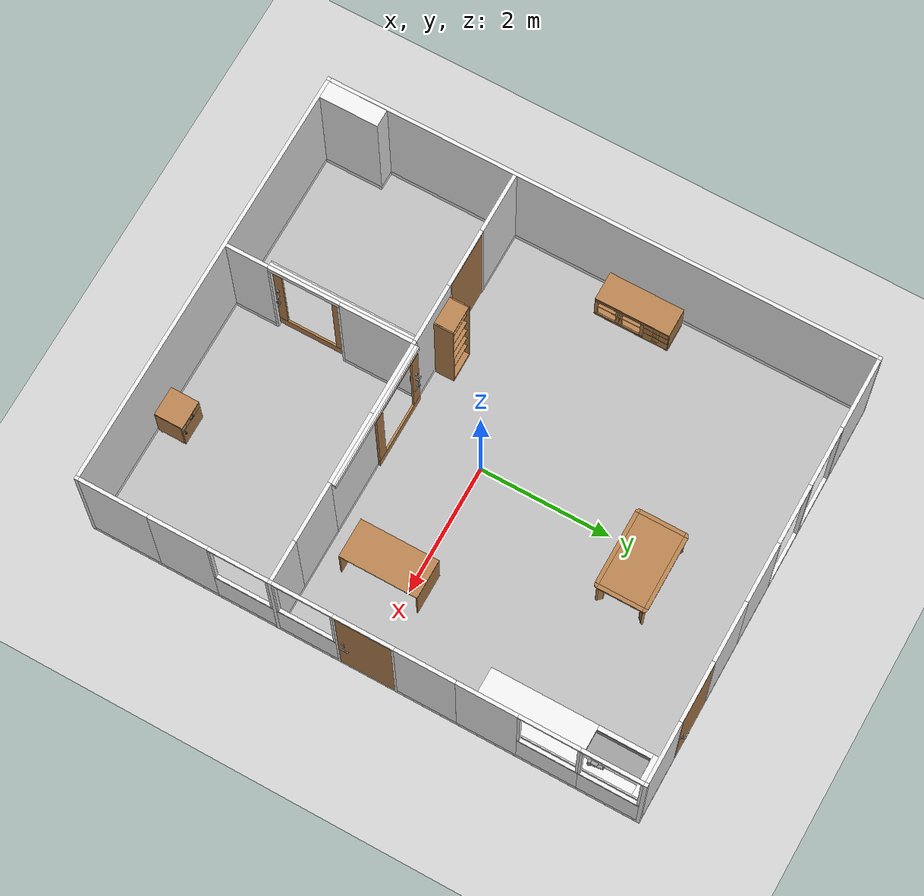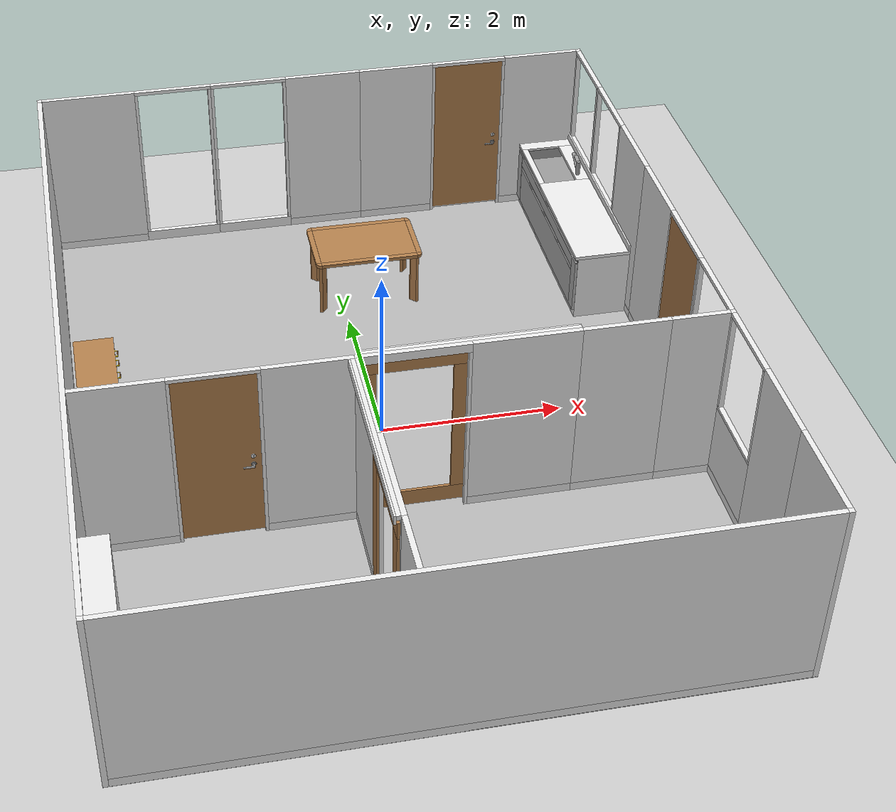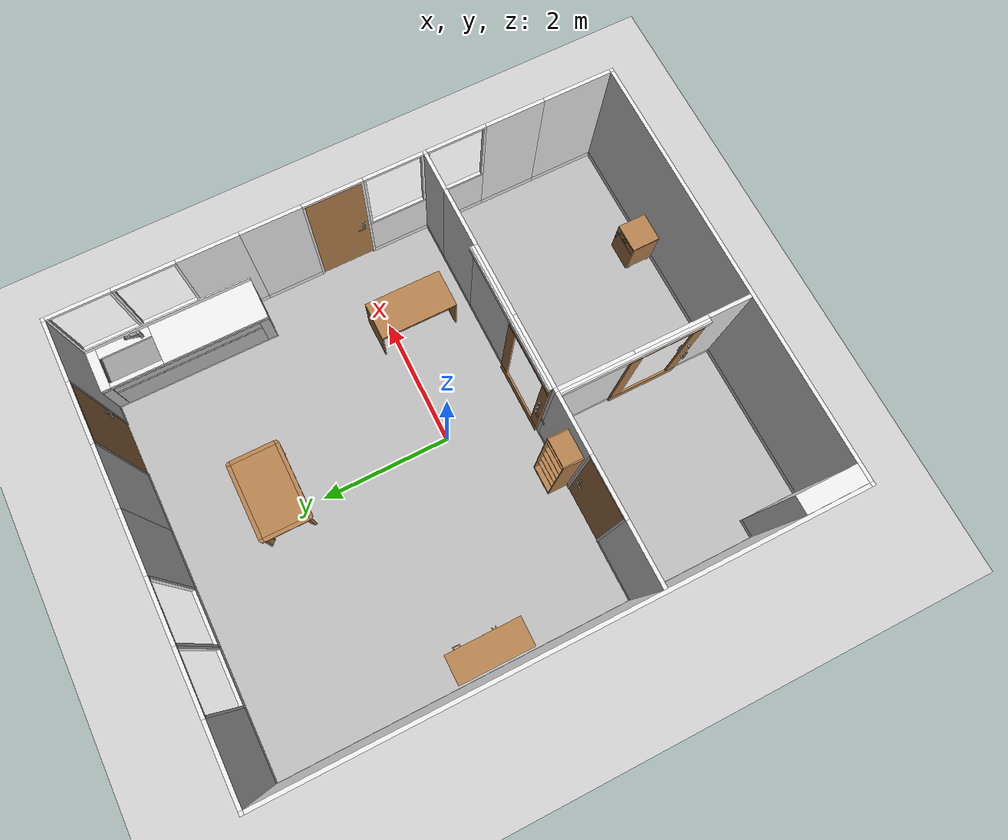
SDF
<sdf version="1.7">
 <world name="default">
  <scene>
   <ambient>0.5 0.5 0.5 1</ambient>
   <shadows>0</shadows>
   <grid>1</grid>
   <background>0.7 0.7 0.7 1</background>
  </scene>
  <physics type="ode">
   <max_step_size>0.001</max_step_size>
   <real_time_factor>1</real_time_factor>
   <real_time_update_rate>1000</real_time_update_rate>
  </physics>
  <model name="ground_plane">
   <static>1</static>
   <link name="link">
    <collision name="collision">
     <geometry><plane><normal>0 0 1</normal><size>100 100</size></plane></geometry>
     <surface>
      <contact><collide_bitmask>65535</collide_bitmask></contact>
      <friction><ode><mu>100</mu><mu2>50</mu2></ode></friction>
     </surface>
    </collision>
    <visual name="visual">
     <cast_shadows>0</cast_shadows>
     <geometry><plane><normal>0 0 1</normal><size>100 100</size></plane></geometry>
     <material>
      <script><uri>file://media/materials/scripts/gazebo.material</uri><name>Gazebo/Grey</name></script>
     </material>
    </visual>
   </link>
  </model>
  <model name="gplane">
   <pose>0 0 0.001 0 -0 0</pose>
   <link name="body">
    <visual name="gplane_vis">
     <geometry><plane><normal>0 0 1</normal><size>6.585 8.405</size></plane></geometry>
     <material>
      <script>
       <uri>model://base_materials/carpet/scripts</uri>
       <uri>model://base_materials/carpet/textures</uri>
       <name>carpet/carpet01</name>
      </script>
     </material>
     <cast_shadows>0</cast_shadows>
    </visual>
    <velocity_decay><linear>0</linear><angular>0</angular></velocity_decay>
   </link>
   <static>1</static>
  </model>
  <light name="inner_point_white1" type="point">
   <pose>1.5 1.2 4 0 -0 0</pose>
   <diffuse>0.2 0.2 0.2 1</diffuse>
   <specular>0.1 0.1 0.1 1</specular>
   <attenuation>
    <range>20</range>
    <linear>0.1</linear>
    <constant>0.2</constant>
    <quadratic>0</quadratic>
   </attenuation>
   <cast_shadows>0</cast_shadows>
   <direction>0 0 -1</direction>
   <spot><inner_angle>0</inner_angle><outer_angle>0</outer_angle><falloff>0</falloff></spot>
  </light>
  <light name="inner_point_white2" type="point">
   <pose>-1.5 1.2 4 0 -0 0</pose>
   <diffuse>0.2 0.2 0.2 1</diffuse>
   <specular>0.1 0.1 0.1 1</specular>
   <attenuation>
    <range>20</range>
    <linear>0.1</linear>
    <constant>0.2</constant>
    <quadratic>0</quadratic>
   </attenuation>
   <cast_shadows>0</cast_shadows>
   <direction>0 0 -1</direction>
   <spot><inner_angle>0</inner_angle><outer_angle>0</outer_angle><falloff>0</falloff></spot>
  </light>
  <light name="inner_point_white3" type="point">
   <pose>1.5 -2.5 4 0 -0 0</pose>
   <diffuse>0.2 0.2 0.2 1</diffuse>
   <specular>0.1 0.1 0.1 1</specular>
   <attenuation>
    <range>20</range>
    <linear>0.1</linear>
    <constant>0.2</constant>
    <quadratic>0</quadratic>
   </attenuation>
   <cast_shadows>0</cast_shadows>
   <direction>0 0 -1</direction>
   <spot><inner_angle>0</inner_angle><outer_angle>0</outer_angle><falloff>0</falloff></spot>
  </light>
  <light name="inner_point_white4" type="point">
   <pose>-1.5 -2.5 4 0 -0 0</pose>
   <diffuse>0.2 0.2 0.2 1</diffuse>
   <specular>0.1 0.1 0.1 1</specular>
   <attenuation>
    <range>20</range>
    <linear>0.1</linear>
    <constant>0.2</constant>
    <quadratic>0</quadratic>
   </attenuation>
   <cast_shadows>0</cast_shadows>
   <direction>0 0 -1</direction>
   <spot><inner_angle>0</inner_angle><outer_angle>0</outer_angle><falloff>0</falloff></spot>
  </light>
  <model name="wall_front_a">
   <link name="link">
    <inertial>
     <mass>50</mass>
     <inertia><ixx>1</ixx><ixy>0</ixy><ixz>0</ixz><iyy>1</iyy><iyz>0</iyz><izz>1</izz></inertia>
    </inertial>
    <visual name="_frame">
     <pose>0 0 1.045 0 -0 0</pose>
     <geometry><box><size>0.055 0.055 2.09</size></box></geometry>
     <material>
      <script><uri>model://base_materials/color/scripts</uri><name>hsr_color/white</name></script>
     </material>
    </visual>
    <collision name="collision_frame">
     <pose>0 0 1.045 0 -0 0</pose>
     <geometry><box><size>0.055 0.055 2.09</size></box></geometry>
    </collision>
    <velocity_decay><linear>0</linear><angular>0</angular></velocity_decay>
   </link>
   <static>1</static>
   <pose>3.265 4.175 0 0 -0 0</pose>
  </model>
  <model name="wall_front_b">
   <link name="link">
    <inertial>
     <mass>50</mass>
     <inertia><ixx>1</ixx><ixy>0</ixy><ixz>0</ixz><iyy>1</iyy><iyz>0</iyz><izz>1</izz></inertia>
    </inertial>
    <visual name="bottom_frame">
     <pose>0 0 0.05 0 -0 0</pose>
     <geometry><box><size>0.055 0.9 0.1</size></box></geometry>
     <material>
      <script><uri>model://base_materials/color/scripts</uri><name>hsr_color/white</name></script>
     </material>
    </visual>
    <collision name="collision_bottom_frame">
     <pose>0 0 0.05 0 -0 0</pose>
     <geometry><box><size>0.055 0.9 0.1</size></box></geometry>
    </collision>
    <visual name="wall">
     <pose>0 0 0.4875 0 -0 0</pose>
     <geometry><box><size>0.055 0.9 0.775</size></box></geometry>
     <material>
      <script>
       <uri>model://base_materials/wall/scripts</uri>
       <uri>model://base_materials/wall/textures</uri>
       <name>wall/white_noise</name>
      </script>
     </material>
    </visual>
    <collision name="collision_wall">
     <pose>0 0 0.4875 0 -0 0</pose>
     <geometry><box><size>0.055 0.9 0.775</size></box></geometry>
    </collision>
    <visual name="center_frame">
     <pose>0 0 0.8925 0 -0 0</pose>
     <geometry><box><size>0.055 0.9 0.035</size></box></geometry>
     <material>
      <script><uri>model://base_materials/color/scripts</uri><name>hsr_color/white</name></script>
     </material>
    </visual>
    <collision name="collision_center_frame">
     <pose>0 0 0.8925 0 -0 0</pose>
     <geometry><box><size>0.055 0.9 0.035</size></box></geometry>
    </collision>
    <visual name="right_frame">
     <pose>0 0.4325 1.48 0 -0 0</pose>
     <geometry><box><size>0.055 0.035 1.14</size></box></geometry>
     <material>
      <script><uri>model://base_materials/color/scripts</uri><name>hsr_color/white</name></script>
     </material>
    </visual>
    <collision name="collision_right_frame">
     <pose>0 0.4325 1.48 0 -0 0</pose>
     <geometry><box><size>0.055 0.035 1.14</size></box></geometry>
    </collision>
    <visual name="left_frame">
     <pose>0 -0.4325 1.48 0 -0 0</pose>
     <geometry><box><size>0.055 0.035 1.14</size></box></geometry>
     <material>
      <script><uri>model://base_materials/color/scripts</uri><name>hsr_color/white</name></script>
     </material>
    </visual>
    <collision name="collision_left_frame">
     <pose>0 -0.4325 1.48 0 -0 0</pose>
     <geometry><box><size>0.055 0.035 1.14</size></box></geometry>
    </collision>
    <visual name="top_frame">
     <pose>0 0 2.07 0 -0 0</pose>
     <geometry><box><size>0.055 0.9 0.04</size></box></geometry>
     <material>
      <script><uri>model://base_materials/color/scripts</uri><name>hsr_color/white</name></script>
     </material>
    </visual>
    <collision name="collision_top_frame">
     <pose>0 0 2.07 0 -0 0</pose>
     <geometry><box><size>0.055 0.9 0.04</size></box></geometry>
    </collision>
    <velocity_decay><linear>0</linear><angular>0</angular></velocity_decay>
   </link>
   <static>1</static>
   <pose>3.265 3.698 0 0 -0 0</pose>
  </model>
  <model name="wall_front_c">
   <link name="link">
    <inertial>
     <mass>50</mass>
     <inertia><ixx>1</ixx><ixy>0</ixy><ixz>0</ixz><iyy>1</iyy><iyz>0</iyz><izz>1</izz></inertia>
    </inertial>
    <visual name="bottom_frame">
     <pose>0 0 0.05 0 -0 0</pose>
     <geometry><box><size>0.055 0.9 0.1</size></box></geometry>
     <material>
      <script><uri>model://base_materials/color/scripts</uri><name>hsr_color/white</name></script>
     </material>
    </visual>
    <collision name="collision_bottom_frame">
     <pose>0 0 0.05 0 -0 0</pose>
     <geometry><box><size>0.055 0.9 0.1</size></box></geometry>
    </collision>
    <visual name="wall">
     <pose>0 0 0.4875 0 -0 0</pose>
     <geometry><box><size>0.055 0.9 0.775</size></box></geometry>
     <material>
      <script>
       <uri>model://base_materials/wall/scripts</uri>
       <uri>model://base_materials/wall/textures</uri>
       <name>wall/white_noise</name>
      </script>
     </material>
    </visual>
    <collision name="collision_wall">
     <pose>0 0 0.4875 0 -0 0</pose>
     <geometry><box><size>0.055 0.9 0.775</size></box></geometry>
    </collision>
    <visual name="center_frame">
     <pose>0 0 0.8925 0 -0 0</pose>
     <geometry><box><size>0.055 0.9 0.035</size></box></geometry>
     <material>
      <script><uri>model://base_materials/color/scripts</uri><name>hsr_color/white</name></script>
     </material>
    </visual>
    <collision name="collision_center_frame">
     <pose>0 0 0.8925 0 -0 0</pose>
     <geometry><box><size>0.055 0.9 0.035</size></box></geometry>
    </collision>
    <visual name="right_frame">
     <pose>0 0.4325 1.48 0 -0 0</pose>
     <geometry><box><size>0.055 0.035 1.14</size></box></geometry>
     <material>
      <script><uri>model://base_materials/color/scripts</uri><name>hsr_color/white</name></script>
     </material>
    </visual>
    <collision name="collision_right_frame">
     <pose>0 0.4325 1.48 0 -0 0</pose>
     <geometry><box><size>0.055 0.035 1.14</size></box></geometry>
    </collision>
    <visual name="left_frame">
     <pose>0 -0.4325 1.48 0 -0 0</pose>
     <geometry><box><size>0.055 0.035 1.14</size></box></geometry>
     <material>
      <script><uri>model://base_materials/color/scripts</uri><name>hsr_color/white</name></script>
     </material>
    </visual>
    <collision name="collision_left_frame">
     <pose>0 -0.4325 1.48 0 -0 0</pose>
     <geometry><box><size>0.055 0.035 1.14</size></box></geometry>
    </collision>
    <visual name="top_frame">
     <pose>0 0 2.07 0 -0 0</pose>
     <geometry><box><size>0.055 0.9 0.04</size></box></geometry>
     <material>
      <script><uri>model://base_materials/color/scripts</uri><name>hsr_color/white</name></script>
     </material>
    </visual>
    <collision name="collision_top_frame">
     <pose>0 0 2.07 0 -0 0</pose>
     <geometry><box><size>0.055 0.9 0.04</size></box></geometry>
    </collision>
    <velocity_decay><linear>0</linear><angular>0</angular></velocity_decay>
   </link>
   <static>1</static>
   <pose>3.265 2.798 0 0 -0 0</pose>
  </model>
  <model name="wall_front_d">
   <link name="link">
    <inertial>
     <mass>50</mass>
     <inertia><ixx>1</ixx><ixy>0</ixy><ixz>0</ixz><iyy>1</iyy><iyz>0</iyz><izz>1</izz></inertia>
    </inertial>
    <visual name="bottom_frame">
     <pose>0 0 0.05 0 -0 0</pose>
     <geometry><box><size>0.055 0.9 0.1</size></box></geometry>
     <material>
      <script><uri>model://base_materials/color/scripts</uri><name>hsr_color/white</name></script>
     </material>
    </visual>
    <collision name="collision_bottom_frame">
     <pose>0 0 0.05 0 -0 0</pose>
     <geometry><box><size>0.055 0.9 0.1</size></box></geometry>
    </collision>
    <visual name="wall">
     <pose>0 0 1.095 0 -0 0</pose>
     <geometry><box><size>0.055 0.9 1.99</size></box></geometry>
     <material>
      <script>
       <uri>model://base_materials/wall/scripts</uri>
       <uri>model://base_materials/wall/textures</uri>
       <name>wall/white_noise</name>
      </script>
     </material>
    </visual>
    <collision name="collision_wall">
     <pose>0 0 1.095 0 -0 0</pose>
     <geometry><box><size>0.055 0.9 1.99</size></box></geometry>
    </collision>
    <velocity_decay><linear>0</linear><angular>0</angular></velocity_decay>
   </link>
   <static>1</static>
   <pose>3.265 1.898 0 0 -0 0</pose>
  </model>
  <model name="wall_front_e">
   <link name="link">
    <inertial>
     <mass>50</mass>
     <inertia><ixx>1</ixx><ixy>0</ixy><ixz>0</ixz><iyy>1</iyy><iyz>0</iyz><izz>1</izz></inertia>
    </inertial>
    <visual name="bottom_frame">
     <pose>0 0 0.05 0 -0 0</pose>
     <geometry><box><size>0.055 0.9 0.1</size></box></geometry>
     <material>
      <script><uri>model://base_materials/color/scripts</uri><name>hsr_color/white</name></script>
     </material>
    </visual>
    <collision name="collision_bottom_frame">
     <pose>0 0 0.05 0 -0 0</pose>
     <geometry><box><size>0.055 0.9 0.1</size></box></geometry>
    </collision>
    <visual name="wall">
     <pose>0 0 1.095 0 -0 0</pose>
     <geometry><box><size>0.055 0.9 1.99</size></box></geometry>
     <material>
      <script>
       <uri>model://base_materials/wall/scripts</uri>
       <uri>model://base_materials/wall/textures</uri>
       <name>wall/white_noise</name>
      </script>
     </material>
    </visual>
    <collision name="collision_wall">
     <pose>0 0 1.095 0 -0 0</pose>
     <geometry><box><size>0.055 0.9 1.99</size></box></geometry>
    </collision>
    <velocity_decay><linear>0</linear><angular>0</angular></velocity_decay>
   </link>
   <static>1</static>
   <pose>3.265 0.9975 0 0 -0 0</pose>
  </model>
  <model name="wall_front_f">
   <link name="link">
    <pose>0 0.45 0 0 -0 0</pose>
    <inertial>
     <mass>50</mass>
     <inertia><ixx>1</ixx><ixy>0</ixy><ixz>0</ixz><iyy>1</iyy><iyz>0</iyz><izz>1</izz></inertia>
    </inertial>
    <visual name="door">
     <pose>0 0 1.05 0 -0 0</pose>
     <geometry><box><size>0.055 0.83 2</size></box></geometry>
     <material>
      <script><uri>model://base_materials/wood/scripts/wood.material</uri><name>base_materials/wood</name></script>
     </material>
    </visual>
    <collision name="collision_door">
     <pose>0 0 1.05 0 -0 0</pose>
     <geometry><box><size>0.055 0.83 2</size></box></geometry>
    </collision>
    <visual name="right_frame">
     <pose>0 0.4325 1.025 0 -0 0</pose>
     <geometry><box><size>0.055 0.035 2.05</size></box></geometry>
     <material>
      <script><uri>model://base_materials/color/scripts</uri><name>hsr_color/white</name></script>
     </material>
    </visual>
    <collision name="collision_right_frame">
     <pose>0 0.4325 1.025 0 -0 0</pose>
     <geometry><box><size>0.055 0.035 2.05</size></box></geometry>
    </collision>
    <visual name="left_frame">
     <pose>0 -0.4325 1.025 0 -0 0</pose>
     <geometry><box><size>0.055 0.035 2.05</size></box></geometry>
     <material>
      <script><uri>model://base_materials/color/scripts</uri><name>hsr_color/white</name></script>
     </material>
    </visual>
    <collision name="collision_left_frame">
     <pose>0 -0.4325 1.025 0 -0 0</pose>
     <geometry><box><size>0.055 0.035 2.05</size></box></geometry>
    </collision>
    <visual name="top_frame">
     <pose>0 0 2.07 0 -0 0</pose>
     <geometry><box><size>0.055 0.9 0.04</size></box></geometry>
     <material>
      <script><uri>model://base_materials/color/scripts</uri><name>hsr_color/white</name></script>
     </material>
    </visual>
    <collision name="collision_top_frame">
     <pose>0 0 2.07 0 -0 0</pose>
     <geometry><box><size>0.055 0.9 0.04</size></box></geometry>
    </collision>
    <visual name="handle_front">
     <pose>0.0775 0.285 0.93 1.5708 -0 0</pose>
     <geometry><cylinder><radius>0.01</radius><length>0.1</length></cylinder></geometry>
     <material>
      <script><uri>model://base_materials/color/scripts</uri><name>hsr_color/grey</name></script>
     </material>
    </visual>
    <collision name="collision_handle_front">
     <pose>0.0775 0.285 0.93 1.5708 -0 0</pose>
     <geometry><cylinder><radius>0.01</radius><length>0.1</length></cylinder></geometry>
    </collision>
    <visual name="handle_back">
     <pose>-0.0775 0.285 0.93 1.5708 -0 0</pose>
     <geometry><cylinder><radius>0.01</radius><length>0.1</length></cylinder></geometry>
     <material>
      <script><uri>model://base_materials/color/scripts</uri><name>hsr_color/grey</name></script>
     </material>
    </visual>
    <collision name="collision_handle_back">
     <pose>-0.0775 0.285 0.93 1.5708 -0 0</pose>
     <geometry><cylinder><radius>0.01</radius><length>0.1</length></cylinder></geometry>
    </collision>
    <visual name="handle_center1">
     <pose>0 0.335 0.93 3.14159 1.57079 3.14159</pose>
     <geometry><cylinder><radius>0.01</radius><length>0.155</length></cylinder></geometry>
     <material>
      <script><uri>model://base_materials/color/scripts</uri><name>hsr_color/grey</name></script>
     </material>
    </visual>
    <collision name="collision_center1">
     <pose>0 0.335 0.93 3.14159 1.57079 3.14159</pose>
     <geometry><cylinder><radius>0.01</radius><length>0.155</length></cylinder></geometry>
    </collision>
    <visual name="handle_center2">
     <pose>0 0.335 0.93 3.14159 1.57079 3.14159</pose>
     <geometry><cylinder><radius>0.025</radius><length>0.075</length></cylinder></geometry>
     <material>
      <script><uri>model://base_materials/color/scripts</uri><name>hsr_color/grey</name></script>
     </material>
    </visual>
    <collision name="collision_center2">
     <pose>0 0.335 0.93 3.14159 1.57079 3.14159</pose>
     <geometry><cylinder><radius>0.025</radius><length>0.075</length></cylinder></geometry>
    </collision>
    <visual name="handle_front_right_corner">
     <pose>0.0775 0.335 0.93 0 -0 0</pose>
     <geometry><sphere><radius>0.01</radius></sphere></geometry>
     <material>
      <script><uri>model://base_materials/color/scripts</uri><name>hsr_color/grey</name></script>
     </material>
    </visual>
    <collision name="collision_handle_front_right_corner">
     <pose>0.0775 0.335 0.93 0 -0 0</pose>
     <geometry><sphere><radius>0.01</radius></sphere></geometry>
    </collision>
    <visual name="handle_front_left_corner">
     <pose>0.0775 0.235 0.93 0 -0 0</pose>
     <geometry><sphere><radius>0.01</radius></sphere></geometry>
     <material>
      <script><uri>model://base_materials/color/scripts</uri><name>hsr_color/grey</name></script>
     </material>
    </visual>
    <collision name="collision_handle_front_left_corner">
     <pose>0.0775 0.235 0.93 0 -0 0</pose>
     <geometry><sphere><radius>0.01</radius></sphere></geometry>
    </collision>
    <visual name="handle_back_right_corner">
     <pose>-0.0775 0.335 0.93 0 -0 0</pose>
     <geometry><sphere><radius>0.01</radius></sphere></geometry>
     <material>
      <script><uri>model://base_materials/color/scripts</uri><name>hsr_color/grey</name></script>
     </material>
    </visual>
    <collision name="collision_handle_back_right_corner">
     <pose>-0.0775 0.335 0.93 0 -0 0</pose>
     <geometry><sphere><radius>0.01</radius></sphere></geometry>
    </collision>
    <visual name="handle_back_left_corner">
     <pose>-0.0775 0.235 0.93 0 -0 0</pose>
     <geometry><sphere><radius>0.01</radius></sphere></geometry>
     <material>
      <script><uri>model://base_materials/color/scripts</uri><name>hsr_color/white</name></script>
     </material>
    </visual>
    <collision name="collision_handle_back_left_corner">
     <pose>-0.0775 0.235 0.93 0 -0 0</pose>
     <geometry><sphere><radius>0.01</radius></sphere></geometry>
    </collision>
    <visual name="handle_lock1">
     <pose>0 0.335 1.03 0 -0 0</pose>
     <geometry><box><size>0.075 0.005 0.04</size></box></geometry>
     <material>
      <script><uri>model://base_materials/color/scripts</uri><name>hsr_color/white</name></script>
     </material>
    </visual>
    <collision name="collision_handle_lock1">
     <pose>0 0.335 1.03 0 -0 0</pose>
     <geometry><box><size>0.075 0.005 0.04</size></box></geometry>
    </collision>
    <visual name="handle_lock2">
     <pose>0 0.335 1.03 3.14159 1.57079 3.14159</pose>
     <geometry><cylinder><radius>0.025</radius><length>0.065</length></cylinder></geometry>
     <material>
      <script><uri>model://base_materials/color/scripts</uri><name>hsr_color/white</name></script>
     </material>
    </visual>
    <collision name="collision_handle_lock2">
     <pose>0 0.335 1.03 3.14159 1.57079 3.14159</pose>
     <geometry><cylinder><radius>0.025</radius><length>0.065</length></cylinder></geometry>
    </collision>
    <velocity_decay><linear>0</linear><angular>0</angular></velocity_decay>
   </link>
   <static>1</static>
   <pose>3.265 0.5475 0 0 -0 3.14159</pose>
  </model>
  <model name="wall_front_g">
   <link name="link">
    <inertial>
     <mass>50</mass>
     <inertia><ixx>1</ixx><ixy>0</ixy><ixz>0</ixz><iyy>1</iyy><iyz>0</iyz><izz>1</izz></inertia>
    </inertial>
    <visual name="bottom_frame">
     <pose>0 0 0.05 0 -0 0</pose>
     <geometry><box><size>0.055 0.9 0.1</size></box></geometry>
     <material>
      <script><uri>model://base_materials/color/scripts</uri><name>hsr_color/white</name></script>
     </material>
    </visual>
    <collision name="collision_bottom_frame">
     <pose>0 0 0.05 0 -0 0</pose>
     <geometry><box><size>0.055 0.9 0.1</size></box></geometry>
    </collision>
    <visual name="wall">
     <pose>0 0 0.4875 0 -0 0</pose>
     <geometry><box><size>0.055 0.9 0.775</size></box></geometry>
     <material>
      <script>
       <uri>model://base_materials/wall/scripts</uri>
       <uri>model://base_materials/wall/textures</uri>
       <name>wall/white_noise</name>
      </script>
     </material>
    </visual>
    <collision name="collision_wall">
     <pose>0 0 0.4875 0 -0 0</pose>
     <geometry><box><size>0.055 0.9 0.775</size></box></geometry>
    </collision>
    <visual name="center_frame">
     <pose>0 0 0.8925 0 -0 0</pose>
     <geometry><box><size>0.055 0.9 0.035</size></box></geometry>
     <material>
      <script><uri>model://base_materials/color/scripts</uri><name>hsr_color/white</name></script>
     </material>
    </visual>
    <collision name="collision_center_frame">
     <pose>0 0 0.8925 0 -0 0</pose>
     <geometry><box><size>0.055 0.9 0.035</size></box></geometry>
    </collision>
    <visual name="right_frame">
     <pose>0 0.4325 1.48 0 -0 0</pose>
     <geometry><box><size>0.055 0.035 1.14</size></box></geometry>
     <material>
      <script><uri>model://base_materials/color/scripts</uri><name>hsr_color/white</name></script>
     </material>
    </visual>
    <collision name="collision_right_frame">
     <pose>0 0.4325 1.48 0 -0 0</pose>
     <geometry><box><size>0.055 0.035 1.14</size></box></geometry>
    </collision>
    <visual name="left_frame">
     <pose>0 -0.4325 1.48 0 -0 0</pose>
     <geometry><box><size>0.055 0.035 1.14</size></box></geometry>
     <material>
      <script><uri>model://base_materials/color/scripts</uri><name>hsr_color/white</name></script>
     </material>
    </visual>
    <collision name="collision_left_frame">
     <pose>0 -0.4325 1.48 0 -0 0</pose>
     <geometry><box><size>0.055 0.035 1.14</size></box></geometry>
    </collision>
    <visual name="top_frame">
     <pose>0 0 2.07 0 -0 0</pose>
     <geometry><box><size>0.055 0.9 0.04</size></box></geometry>
     <material>
      <script><uri>model://base_materials/color/scripts</uri><name>hsr_color/white</name></script>
     </material>
    </visual>
    <collision name="collision_top_frame">
     <pose>0 0 2.07 0 -0 0</pose>
     <geometry><box><size>0.055 0.9 0.04</size></box></geometry>
    </collision>
    <velocity_decay><linear>0</linear><angular>0</angular></velocity_decay>
   </link>
   <static>1</static>
   <pose>3.265 -0.8025 0 0 -0 0</pose>
  </model>
  <model name="wall_front_h">
   <link name="link">
    <inertial>
     <mass>50</mass>
     <inertia><ixx>1</ixx><ixy>0</ixy><ixz>0</ixz><iyy>1</iyy><iyz>0</iyz><izz>1</izz></inertia>
    </inertial>
    <visual name="_frame">
     <pose>0 0 1.045 0 -0 0</pose>
     <geometry><box><size>0.055 0.055 2.09</size></box></geometry>
     <material>
      <script><uri>model://base_materials/color/scripts</uri><name>hsr_color/white</name></script>
     </material>
    </visual>
    <collision name="collision_frame">
     <pose>0 0 1.045 0 -0 0</pose>
     <geometry><box><size>0.055 0.055 2.09</size></box></geometry>
    </collision>
    <velocity_decay><linear>0</linear><angular>0</angular></velocity_decay>
   </link>
   <static>1</static>
   <pose>3.265 -1.28 0 0 -0 0</pose>
  </model>
  <model name="wall_front_i">
   <link name="link">
    <inertial>
     <mass>50</mass>
     <inertia><ixx>1</ixx><ixy>0</ixy><ixz>0</ixz><iyy>1</iyy><iyz>0</iyz><izz>1</izz></inertia>
    </inertial>
    <visual name="bottom_frame">
     <pose>0 0 0.05 0 -0 0</pose>
     <geometry><box><size>0.055 0.9 0.1</size></box></geometry>
     <material>
      <script><uri>model://base_materials/color/scripts</uri><name>hsr_color/white</name></script>
     </material>
    </visual>
    <collision name="collision_bottom_frame">
     <pose>0 0 0.05 0 -0 0</pose>
     <geometry><box><size>0.055 0.9 0.1</size></box></geometry>
    </collision>
    <visual name="wall">
     <pose>0 0 0.4875 0 -0 0</pose>
     <geometry><box><size>0.055 0.9 0.775</size></box></geometry>
     <material>
      <script>
       <uri>model://base_materials/wall/scripts</uri>
       <uri>model://base_materials/wall/textures</uri>
       <name>wall/white_noise</name>
      </script>
     </material>
    </visual>
    <collision name="collision_wall">
     <pose>0 0 0.4875 0 -0 0</pose>
     <geometry><box><size>0.055 0.9 0.775</size></box></geometry>
    </collision>
    <visual name="center_frame">
     <pose>0 0 0.8925 0 -0 0</pose>
     <geometry><box><size>0.055 0.9 0.035</size></box></geometry>
     <material>
      <script><uri>model://base_materials/color/scripts</uri><name>hsr_color/white</name></script>
     </material>
    </visual>
    <collision name="collision_center_frame">
     <pose>0 0 0.8925 0 -0 0</pose>
     <geometry><box><size>0.055 0.9 0.035</size></box></geometry>
    </collision>
    <visual name="right_frame">
     <pose>0 0.4325 1.48 0 -0 0</pose>
     <geometry><box><size>0.055 0.035 1.14</size></box></geometry>
     <material>
      <script><uri>model://base_materials/color/scripts</uri><name>hsr_color/white</name></script>
     </material>
    </visual>
    <collision name="collision_right_frame">
     <pose>0 0.4325 1.48 0 -0 0</pose>
     <geometry><box><size>0.055 0.035 1.14</size></box></geometry>
    </collision>
    <visual name="left_frame">
     <pose>0 -0.4325 1.48 0 -0 0</pose>
     <geometry><box><size>0.055 0.035 1.14</size></box></geometry>
     <material>
      <script><uri>model://base_materials/color/scripts</uri><name>hsr_color/white</name></script>
     </material>
    </visual>
    <collision name="collision_left_frame">
     <pose>0 -0.4325 1.48 0 -0 0</pose>
     <geometry><box><size>0.055 0.035 1.14</size></box></geometry>
    </collision>
    <visual name="top_frame">
     <pose>0 0 2.07 0 -0 0</pose>
     <geometry><box><size>0.055 0.9 0.04</size></box></geometry>
     <material>
      <script><uri>model://base_materials/color/scripts</uri><name>hsr_color/white</name></script>
     </material>
    </visual>
    <collision name="collision_top_frame">
     <pose>0 0 2.07 0 -0 0</pose>
     <geometry><box><size>0.055 0.9 0.04</size></box></geometry>
    </collision>
    <velocity_decay><linear>0</linear><angular>0</angular></velocity_decay>
   </link>
   <static>1</static>
   <pose>3.265 -1.7575 0 0 -0 0</pose>
  </model>
  <model name="wall_front_j">
   <link name="link">
    <inertial>
     <mass>50</mass>
     <inertia><ixx>1</ixx><ixy>0</ixy><ixz>0</ixz><iyy>1</iyy><iyz>0</iyz><izz>1</izz></inertia>
    </inertial>
    <visual name="bottom_frame">
     <pose>0 0 0.05 0 -0 0</pose>
     <geometry><box><size>0.055 0.9 0.1</size></box></geometry>
     <material>
      <script><uri>model://base_materials/color/scripts</uri><name>hsr_color/white</name></script>
     </material>
    </visual>
    <collision name="collision_bottom_frame">
     <pose>0 0 0.05 0 -0 0</pose>
     <geometry><box><size>0.055 0.9 0.1</size></box></geometry>
    </collision>
    <visual name="wall">
     <pose>0 0 1.095 0 -0 0</pose>
     <geometry><box><size>0.055 0.9 1.99</size></box></geometry>
     <material>
      <script>
       <uri>model://base_materials/wall/scripts</uri>
       <uri>model://base_materials/wall/textures</uri>
       <name>wall/white_noise</name>
      </script>
     </material>
    </visual>
    <collision name="collision_wall">
     <pose>0 0 1.095 0 -0 0</pose>
     <geometry><box><size>0.055 0.9 1.99</size></box></geometry>
    </collision>
    <velocity_decay><linear>0</linear><angular>0</angular></velocity_decay>
   </link>
   <static>1</static>
   <pose>3.265 -2.6575 0 0 -0 0</pose>
  </model>
  <model name="wall_front_k">
   <link name="link">
    <inertial>
     <mass>50</mass>
     <inertia><ixx>1</ixx><ixy>0</ixy><ixz>0</ixz><iyy>1</iyy><iyz>0</iyz><izz>1</izz></inertia>
    </inertial>
    <visual name="bottom_frame">
     <pose>0 0 0.05 0 -0 0</pose>
     <geometry><box><size>0.055 1.04 0.1</size></box></geometry>
     <material>
      <script><uri>model://base_materials/color/scripts</uri><name>hsr_color/white</name></script>
     </material>
    </visual>
    <collision name="collision_bottom_frame">
     <pose>0 0 0.05 0 -0 0</pose>
     <geometry><box><size>0.055 1.04 0.1</size></box></geometry>
    </collision>
    <visual name="wall">
     <pose>0 0 1.095 0 -0 0</pose>
     <geometry><box><size>0.055 1.04 1.99</size></box></geometry>
     <material>
      <script>
       <uri>model://base_materials/wall/scripts</uri>
       <uri>model://base_materials/wall/textures</uri>
       <name>wall/white_noise</name>
      </script>
     </material>
    </visual>
    <collision name="collision_wall">
     <pose>0 0 1.095 0 -0 0</pose>
     <geometry><box><size>0.055 1.04 1.99</size></box></geometry>
    </collision>
    <velocity_decay><linear>0</linear><angular>0</angular></velocity_decay>
   </link>
   <static>1</static>
   <pose>3.265 -3.6275 0 0 -0 0</pose>
  </model>
  <model name="wall_front_l">
   <link name="link">
    <inertial>
     <mass>50</mass>
     <inertia><ixx>1</ixx><ixy>0</ixy><ixz>0</ixz><iyy>1</iyy><iyz>0</iyz><izz>1</izz></inertia>
    </inertial>
    <visual name="_frame">
     <pose>0 0 1.045 0 -0 0</pose>
     <geometry><box><size>0.055 0.055 2.09</size></box></geometry>
     <material>
      <script><uri>model://base_materials/color/scripts</uri><name>hsr_color/white</name></script>
     </material>
    </visual>
    <collision name="collision_frame">
     <pose>0 0 1.045 0 -0 0</pose>
     <geometry><box><size>0.055 0.055 2.09</size></box></geometry>
    </collision>
    <velocity_decay><linear>0</linear><angular>0</angular></velocity_decay>
   </link>
   <static>1</static>
   <pose>3.265 -4.175 0 0 -0 0</pose>
  </model>
  <model name="wall_right_a">
   <link name="link">
    <inertial>
     <mass>50</mass>
     <inertia><ixx>1</ixx><ixy>0</ixy><ixz>0</ixz><iyy>1</iyy><iyz>0</iyz><izz>1</izz></inertia>
    </inertial>
    <visual name="bottom_frame">
     <pose>0 0 0.05 0 -0 0</pose>
     <geometry><box><size>0.055 0.9 0.1</size></box></geometry>
     <material>
      <script><uri>model://base_materials/color/scripts</uri><name>hsr_color/white</name></script>
     </material>
    </visual>
    <collision name="collision_bottom_frame">
     <pose>0 0 0.05 0 -0 0</pose>
     <geometry><box><size>0.055 0.9 0.1</size></box></geometry>
    </collision>
    <visual name="wall">
     <pose>0 0 1.095 0 -0 0</pose>
     <geometry><box><size>0.055 0.9 1.99</size></box></geometry>
     <material>
      <script>
       <uri>model://base_materials/wall/scripts</uri>
       <uri>model://base_materials/wall/textures</uri>
       <name>wall/white_noise</name>
      </script>
     </material>
    </visual>
    <collision name="collision_wall">
     <pose>0 0 1.095 0 -0 0</pose>
     <geometry><box><size>0.055 0.9 1.99</size></box></geometry>
    </collision>
    <velocity_decay><linear>0</linear><angular>0</angular></velocity_decay>
   </link>
   <static>1</static>
   <pose>2.788 4.175 0 0 -0 1.5708</pose>
  </model>
  <model name="wall_right_b">
   <link name="link">
    <pose>0 0.45 0 0 -0 0</pose>
    <inertial>
     <mass>50</mass>
     <inertia><ixx>1</ixx><ixy>0</ixy><ixz>0</ixz><iyy>1</iyy><iyz>0</iyz><izz>1</izz></inertia>
    </inertial>
    <visual name="door">
     <pose>0 0 1.05 0 -0 0</pose>
     <geometry><box><size>0.055 0.83 2</size></box></geometry>
     <material>
      <script><uri>model://base_materials/wood/scripts/wood.material</uri><name>base_materials/wood</name></script>
     </material>
    </visual>
    <collision name="collision_door">
     <pose>0 0 1.05 0 -0 0</pose>
     <geometry><box><size>0.055 0.83 2</size></box></geometry>
    </collision>
    <visual name="right_frame">
     <pose>0 0.4325 1.025 0 -0 0</pose>
     <geometry><box><size>0.055 0.035 2.05</size></box></geometry>
     <material>
      <script><uri>model://base_materials/color/scripts</uri><name>hsr_color/white</name></script>
     </material>
    </visual>
    <collision name="collision_right_frame">
     <pose>0 0.4325 1.025 0 -0 0</pose>
     <geometry><box><size>0.055 0.035 2.05</size></box></geometry>
    </collision>
    <visual name="left_frame">
     <pose>0 -0.4325 1.025 0 -0 0</pose>
     <geometry><box><size>0.055 0.035 2.05</size></box></geometry>
     <material>
      <script><uri>model://base_materials/color/scripts</uri><name>hsr_color/white</name></script>
     </material>
    </visual>
    <collision name="collision_left_frame">
     <pose>0 -0.4325 1.025 0 -0 0</pose>
     <geometry><box><size>0.055 0.035 2.05</size></box></geometry>
    </collision>
    <visual name="top_frame">
     <pose>0 0 2.07 0 -0 0</pose>
     <geometry><box><size>0.055 0.9 0.04</size></box></geometry>
     <material>
      <script><uri>model://base_materials/color/scripts</uri><name>hsr_color/white</name></script>
     </material>
    </visual>
    <collision name="collision_top_frame">
     <pose>0 0 2.07 0 -0 0</pose>
     <geometry><box><size>0.055 0.9 0.04</size></box></geometry>
    </collision>
    <visual name="handle_front">
     <pose>0.0775 0.285 0.93 1.5708 -0 0</pose>
     <geometry><cylinder><radius>0.01</radius><length>0.1</length></cylinder></geometry>
     <material>
      <script><uri>model://base_materials/color/scripts</uri><name>hsr_color/grey</name></script>
     </material>
    </visual>
    <collision name="collision_handle_front">
     <pose>0.0775 0.285 0.93 1.5708 -0 0</pose>
     <geometry><cylinder><radius>0.01</radius><length>0.1</length></cylinder></geometry>
    </collision>
    <visual name="handle_back">
     <pose>-0.0775 0.285 0.93 1.5708 -0 0</pose>
     <geometry><cylinder><radius>0.01</radius><length>0.1</length></cylinder></geometry>
     <material>
      <script><uri>model://base_materials/color/scripts</uri><name>hsr_color/grey</name></script>
     </material>
    </visual>
    <collision name="collision_handle_back">
     <pose>-0.0775 0.285 0.93 1.5708 -0 0</pose>
     <geometry><cylinder><radius>0.01</radius><length>0.1</length></cylinder></geometry>
    </collision>
    <visual name="handle_center1">
     <pose>0 0.335 0.93 3.14159 1.57079 3.14159</pose>
     <geometry><cylinder><radius>0.01</radius><length>0.155</length></cylinder></geometry>
     <material>
      <script><uri>model://base_materials/color/scripts</uri><name>hsr_color/grey</name></script>
     </material>
    </visual>
    <collision name="collision_center1">
     <pose>0 0.335 0.93 3.14159 1.57079 3.14159</pose>
     <geometry><cylinder><radius>0.01</radius><length>0.155</length></cylinder></geometry>
    </collision>
    <visual name="handle_center2">
     <pose>0 0.335 0.93 3.14159 1.57079 3.14159</pose>
     <geometry><cylinder><radius>0.025</radius><length>0.075</length></cylinder></geometry>
     <material>
      <script><uri>model://base_materials/color/scripts</uri><name>hsr_color/grey</name></script>
     </material>
    </visual>
    <collision name="collision_center2">
     <pose>0 0.335 0.93 3.14159 1.57079 3.14159</pose>
     <geometry><cylinder><radius>0.025</radius><length>0.075</length></cylinder></geometry>
    </collision>
    <visual name="handle_front_right_corner">
     <pose>0.0775 0.335 0.93 0 -0 0</pose>
     <geometry><sphere><radius>0.01</radius></sphere></geometry>
     <material>
      <script><uri>model://base_materials/color/scripts</uri><name>hsr_color/grey</name></script>
     </material>
    </visual>
    <collision name="collision_handle_front_right_corner">
     <pose>0.0775 0.335 0.93 0 -0 0</pose>
     <geometry><sphere><radius>0.01</radius></sphere></geometry>
    </collision>
    <visual name="handle_front_left_corner">
     <pose>0.0775 0.235 0.93 0 -0 0</pose>
     <geometry><sphere><radius>0.01</radius></sphere></geometry>
     <material>
      <script><uri>model://base_materials/color/scripts</uri><name>hsr_color/grey</name></script>
     </material>
    </visual>
    <collision name="collision_handle_front_left_corner">
     <pose>0.0775 0.235 0.93 0 -0 0</pose>
     <geometry><sphere><radius>0.01</radius></sphere></geometry>
    </collision>
    <visual name="handle_back_right_corner">
     <pose>-0.0775 0.335 0.93 0 -0 0</pose>
     <geometry><sphere><radius>0.01</radius></sphere></geometry>
     <material>
      <script><uri>model://base_materials/color/scripts</uri><name>hsr_color/grey</name></script>
     </material>
    </visual>
    <collision name="collision_handle_back_right_corner">
     <pose>-0.0775 0.335 0.93 0 -0 0</pose>
     <geometry><sphere><radius>0.01</radius></sphere></geometry>
    </collision>
    <visual name="handle_back_left_corner">
     <pose>-0.0775 0.235 0.93 0 -0 0</pose>
     <geometry><sphere><radius>0.01</radius></sphere></geometry>
     <material>
      <script><uri>model://base_materials/color/scripts</uri><name>hsr_color/white</name></script>
     </material>
    </visual>
    <collision name="collision_handle_back_left_corner">
     <pose>-0.0775 0.235 0.93 0 -0 0</pose>
     <geometry><sphere><radius>0.01</radius></sphere></geometry>
    </collision>
    <visual name="handle_lock1">
     <pose>0 0.335 1.03 0 -0 0</pose>
     <geometry><box><size>0.075 0.005 0.04</size></box></geometry>
     <material>
      <script><uri>model://base_materials/color/scripts</uri><name>hsr_color/white</name></script>
     </material>
    </visual>
    <collision name="collision_handle_lock1">
     <pose>0 0.335 1.03 0 -0 0</pose>
     <geometry><box><size>0.075 0.005 0.04</size></box></geometry>
    </collision>
    <visual name="handle_lock2">
     <pose>0 0.335 1.03 3.14159 1.57079 3.14159</pose>
     <geometry><cylinder><radius>0.025</radius><length>0.065</length></cylinder></geometry>
     <material>
      <script><uri>model://base_materials/color/scripts</uri><name>hsr_color/white</name></script>
     </material>
    </visual>
    <collision name="collision_handle_lock2">
     <pose>0 0.335 1.03 3.14159 1.57079 3.14159</pose>
     <geometry><cylinder><radius>0.025</radius><length>0.065</length></cylinder></geometry>
    </collision>
    <velocity_decay><linear>0</linear><angular>0</angular></velocity_decay>
   </link>
   <static>1</static>
   <pose>1.4375 4.175 0 0 0 -1.5708</pose>
  </model>
  <model name="wall_right_c">
   <link name="link">
    <inertial>
     <mass>50</mass>
     <inertia><ixx>1</ixx><ixy>0</ixy><ixz>0</ixz><iyy>1</iyy><iyz>0</iyz><izz>1</izz></inertia>
    </inertial>
    <visual name="bottom_frame">
     <pose>0 0 0.05 0 -0 0</pose>
     <geometry><box><size>0.055 0.9 0.1</size></box></geometry>
     <material>
      <script><uri>model://base_materials/color/scripts</uri><name>hsr_color/white</name></script>
     </material>
    </visual>
    <collision name="collision_bottom_frame">
     <pose>0 0 0.05 0 -0 0</pose>
     <geometry><box><size>0.055 0.9 0.1</size></box></geometry>
    </collision>
    <visual name="wall">
     <pose>0 0 1.095 0 -0 0</pose>
     <geometry><box><size>0.055 0.9 1.99</size></box></geometry>
     <material>
      <script>
       <uri>model://base_materials/wall/scripts</uri>
       <uri>model://base_materials/wall/textures</uri>
       <name>wall/white_noise</name>
      </script>
     </material>
    </visual>
    <collision name="collision_wall">
     <pose>0 0 1.095 0 -0 0</pose>
     <geometry><box><size>0.055 0.9 1.99</size></box></geometry>
    </collision>
    <velocity_decay><linear>0</linear><angular>0</angular></velocity_decay>
   </link>
   <static>1</static>
   <pose>0.9875 4.175 0 0 -0 1.5708</pose>
  </model>
  <model name="wall_right_d">
   <link name="link">
    <inertial>
     <mass>50</mass>
     <inertia><ixx>1</ixx><ixy>0</ixy><ixz>0</ixz><iyy>1</iyy><iyz>0</iyz><izz>1</izz></inertia>
    </inertial>
    <visual name="bottom_frame">
     <pose>0 0 0.05 0 -0 0</pose>
     <geometry><box><size>0.055 0.9 0.1</size></box></geometry>
     <material>
      <script><uri>model://base_materials/color/scripts</uri><name>hsr_color/white</name></script>
     </material>
    </visual>
    <collision name="collision_bottom_frame">
     <pose>0 0 0.05 0 -0 0</pose>
     <geometry><box><size>0.055 0.9 0.1</size></box></geometry>
    </collision>
    <visual name="wall">
     <pose>0 0 1.095 0 -0 0</pose>
     <geometry><box><size>0.055 0.9 1.99</size></box></geometry>
     <material>
      <script>
       <uri>model://base_materials/wall/scripts</uri>
       <uri>model://base_materials/wall/textures</uri>
       <name>wall/white_noise</name>
      </script>
     </material>
    </visual>
    <collision name="collision_wall">
     <pose>0 0 1.095 0 -0 0</pose>
     <geometry><box><size>0.055 0.9 1.99</size></box></geometry>
    </collision>
    <velocity_decay><linear>0</linear><angular>0</angular></velocity_decay>
   </link>
   <static>1</static>
   <pose>0.0875 4.175 0 0 -0 1.5708</pose>
  </model>
  <model name="wall_right_e">
   <link name="link">
    <inertial>
     <mass>50</mass>
     <inertia><ixx>1</ixx><ixy>0</ixy><ixz>0</ixz><iyy>1</iyy><iyz>0</iyz><izz>1</izz></inertia>
    </inertial>
    <visual name="bottom_frame">
     <pose>0 0 0.065 0 -0 0</pose>
     <geometry><box><size>0.055 0.9 0.13</size></box></geometry>
     <material>
      <script><uri>model://base_materials/color/scripts</uri><name>hsr_color/white</name></script>
     </material>
    </visual>
    <collision name="collision_bottom_frame">
     <pose>0 0 0.065 0 -0 0</pose>
     <geometry><box><size>0.055 0.9 0.13</size></box></geometry>
    </collision>
    <visual name="right_frame">
     <pose>0 0.4325 1.09 0 -0 0</pose>
     <geometry><box><size>0.055 0.035 1.92</size></box></geometry>
     <material>
      <script><uri>model://base_materials/color/scripts</uri><name>hsr_color/white</name></script>
     </material>
    </visual>
    <collision name="collision_right_frame">
     <pose>0 0.4325 1.09 0 -0 0</pose>
     <geometry><box><size>0.055 0.035 1.92</size></box></geometry>
    </collision>
    <visual name="left_frame">
     <pose>0 -0.4325 1.09 0 -0 0</pose>
     <geometry><box><size>0.055 0.035 1.92</size></box></geometry>
     <material>
      <script><uri>model://base_materials/color/scripts</uri><name>hsr_color/white</name></script>
     </material>
    </visual>
    <collision name="collision_left_frame">
     <pose>0 -0.4325 1.09 0 -0 0</pose>
     <geometry><box><size>0.055 0.035 1.92</size></box></geometry>
    </collision>
    <visual name="top_frame">
     <pose>0 0 2.07 0 -0 0</pose>
     <geometry><box><size>0.055 0.9 0.04</size></box></geometry>
     <material>
      <script><uri>model://base_materials/color/scripts</uri><name>hsr_color/white</name></script>
     </material>
    </visual>
    <collision name="collision_top_frame">
     <pose>0 0 2.07 0 -0 0</pose>
     <geometry><box><size>0.055 0.9 0.04</size></box></geometry>
    </collision>
    <velocity_decay><linear>0</linear><angular>0</angular></velocity_decay>
   </link>
   <static>1</static>
   <pose>-0.8125 4.175 0 0 -0 1.5708</pose>
  </model>
  <model name="wall_right_f">
   <link name="link">
    <inertial>
     <mass>50</mass>
     <inertia><ixx>1</ixx><ixy>0</ixy><ixz>0</ixz><iyy>1</iyy><iyz>0</iyz><izz>1</izz></inertia>
    </inertial>
    <visual name="bottom_frame">
     <pose>0 0 0.065 0 -0 0</pose>
     <geometry><box><size>0.055 0.9 0.13</size></box></geometry>
     <material>
      <script><uri>model://base_materials/color/scripts</uri><name>hsr_color/white</name></script>
     </material>
    </visual>
    <collision name="collision_bottom_frame">
     <pose>0 0 0.065 0 -0 0</pose>
     <geometry><box><size>0.055 0.9 0.13</size></box></geometry>
    </collision>
    <visual name="right_frame">
     <pose>0 0.4325 1.09 0 -0 0</pose>
     <geometry><box><size>0.055 0.035 1.92</size></box></geometry>
     <material>
      <script><uri>model://base_materials/color/scripts</uri><name>hsr_color/white</name></script>
     </material>
    </visual>
    <collision name="collision_right_frame">
     <pose>0 0.4325 1.09 0 -0 0</pose>
     <geometry><box><size>0.055 0.035 1.92</size></box></geometry>
    </collision>
    <visual name="left_frame">
     <pose>0 -0.4325 1.09 0 -0 0</pose>
     <geometry><box><size>0.055 0.035 1.92</size></box></geometry>
     <material>
      <script><uri>model://base_materials/color/scripts</uri><name>hsr_color/white</name></script>
     </material>
    </visual>
    <collision name="collision_left_frame">
     <pose>0 -0.4325 1.09 0 -0 0</pose>
     <geometry><box><size>0.055 0.035 1.92</size></box></geometry>
    </collision>
    <visual name="top_frame">
     <pose>0 0 2.07 0 -0 0</pose>
     <geometry><box><size>0.055 0.9 0.04</size></box></geometry>
     <material>
      <script><uri>model://base_materials/color/scripts</uri><name>hsr_color/white</name></script>
     </material>
    </visual>
    <collision name="collision_top_frame">
     <pose>0 0 2.07 0 -0 0</pose>
     <geometry><box><size>0.055 0.9 0.04</size></box></geometry>
    </collision>
    <velocity_decay><linear>0</linear><angular>0</angular></velocity_decay>
   </link>
   <static>1</static>
   <pose>-1.7125 4.175 0 0 -0 1.5708</pose>
  </model>
  <model name="wall_right_g">
   <link name="link">
    <inertial>
     <mass>50</mass>
     <inertia><ixx>1</ixx><ixy>0</ixy><ixz>0</ixz><iyy>1</iyy><iyz>0</iyz><izz>1</izz></inertia>
    </inertial>
    <visual name="bottom_frame">
     <pose>0 0 0.05 0 -0 0</pose>
     <geometry><box><size>0.055 1.075 0.1</size></box></geometry>
     <material>
      <script><uri>model://base_materials/color/scripts</uri><name>hsr_color/white</name></script>
     </material>
    </visual>
    <collision name="collision_bottom_frame">
     <pose>0 0 0.05 0 -0 0</pose>
     <geometry><box><size>0.055 1.075 0.1</size></box></geometry>
    </collision>
    <visual name="wall">
     <pose>0 0 1.095 0 -0 0</pose>
     <geometry><box><size>0.055 1.075 1.99</size></box></geometry>
     <material>
      <script>
       <uri>model://base_materials/wall/scripts</uri>
       <uri>model://base_materials/wall/textures</uri>
       <name>wall/white_noise</name>
      </script>
     </material>
    </visual>
    <collision name="collision_wall">
     <pose>0 0 1.095 0 -0 0</pose>
     <geometry><box><size>0.055 1.075 1.99</size></box></geometry>
    </collision>
    <velocity_decay><linear>0</linear><angular>0</angular></velocity_decay>
   </link>
   <static>1</static>
   <pose>-2.7 4.175 0 0 -0 1.5708</pose>
  </model>
  <model name="wall_back_a">
   <link name="link">
    <inertial>
     <mass>50</mass>
     <inertia><ixx>1</ixx><ixy>0</ixy><ixz>0</ixz><iyy>1</iyy><iyz>0</iyz><izz>1</izz></inertia>
    </inertial>
    <visual name="_frame">
     <pose>0 0 1.045 0 -0 0</pose>
     <geometry><box><size>0.055 0.055 2.09</size></box></geometry>
     <material>
      <script><uri>model://base_materials/color/scripts</uri><name>hsr_color/white</name></script>
     </material>
    </visual>
    <collision name="collision_frame">
     <pose>0 0 1.045 0 -0 0</pose>
     <geometry><box><size>0.055 0.055 2.09</size></box></geometry>
    </collision>
    <velocity_decay><linear>0</linear><angular>0</angular></velocity_decay>
   </link>
   <static>1</static>
   <pose>-3.265 4.175 0 0 -0 0</pose>
  </model>
  <model name="wall_back_b">
   <link name="link">
    <inertial>
     <mass>50</mass>
     <inertia><ixx>1</ixx><ixy>0</ixy><ixz>0</ixz><iyy>1</iyy><iyz>0</iyz><izz>1</izz></inertia>
    </inertial>
    <visual name="bottom_frame">
     <pose>0 0 0.05 0 -0 0</pose>
     <geometry><box><size>0.055 8.295 0.1</size></box></geometry>
     <material>
      <script><uri>model://base_materials/color/scripts</uri><name>hsr_color/white</name></script>
     </material>
    </visual>
    <collision name="collision_bottom_frame">
     <pose>0 0 0.05 0 -0 0</pose>
     <geometry><box><size>0.055 8.295 0.1</size></box></geometry>
    </collision>
    <visual name="wall">
     <pose>0 0 1.095 0 -0 0</pose>
     <geometry><box><size>0.055 8.295 1.99</size></box></geometry>
     <material>
      <script>
       <uri>model://base_materials/wall/scripts</uri>
       <uri>model://base_materials/wall/textures</uri>
       <name>wall/white_noise</name>
      </script>
     </material>
    </visual>
    <collision name="collision_wall">
     <pose>0 0 1.095 0 -0 0</pose>
     <geometry><box><size>0.055 8.295 1.99</size></box></geometry>
    </collision>
    <velocity_decay><linear>0</linear><angular>0</angular></velocity_decay>
   </link>
   <static>1</static>
   <pose>-3.265 0 0 0 -0 0</pose>
  </model>
  <model name="wall_back_c">
   <link name="link">
    <inertial>
     <mass>50</mass>
     <inertia><ixx>1</ixx><ixy>0</ixy><ixz>0</ixz><iyy>1</iyy><iyz>0</iyz><izz>1</izz></inertia>
    </inertial>
    <visual name="_frame">
     <pose>0 0 1.045 0 -0 0</pose>
     <geometry><box><size>0.055 0.055 2.09</size></box></geometry>
     <material>
      <script><uri>model://base_materials/color/scripts</uri><name>hsr_color/white</name></script>
     </material>
    </visual>
    <collision name="collision_frame">
     <pose>0 0 1.045 0 -0 0</pose>
     <geometry><box><size>0.055 0.055 2.09</size></box></geometry>
    </collision>
    <velocity_decay><linear>0</linear><angular>0</angular></velocity_decay>
   </link>
   <static>1</static>
   <pose>-3.265 -4.175 0 0 -0 0</pose>
  </model>
  <model name="wall_left_a">
   <link name="link">
    <inertial>
     <mass>50</mass>
     <inertia><ixx>1</ixx><ixy>0</ixy><ixz>0</ixz><iyy>1</iyy><iyz>0</iyz><izz>1</izz></inertia>
    </inertial>
    <visual name="bottom_frame">
     <pose>0 0 0.05 0 -0 0</pose>
     <geometry><box><size>0.055 6.475 0.1</size></box></geometry>
     <material>
      <script><uri>model://base_materials/color/scripts</uri><name>hsr_color/white</name></script>
     </material>
    </visual>
    <collision name="collision_bottom_frame">
     <pose>0 0 0.05 0 -0 0</pose>
     <geometry><box><size>0.055 6.475 0.1</size></box></geometry>
    </collision>
    <visual name="wall">
     <pose>0 0 1.095 0 -0 0</pose>
     <geometry><box><size>0.055 6.475 1.99</size></box></geometry>
     <material>
      <script>
       <uri>model://base_materials/wall/scripts</uri>
       <uri>model://base_materials/wall/textures</uri>
       <name>wall/white_noise</name>
      </script>
     </material>
    </visual>
    <collision name="collision_wall">
     <pose>0 0 1.095 0 -0 0</pose>
     <geometry><box><size>0.055 6.475 1.99</size></box></geometry>
    </collision>
    <velocity_decay><linear>0</linear><angular>0</angular></velocity_decay>
   </link>
   <static>1</static>
   <pose>0 -4.175 0 0 -0 1.5708</pose>
  </model>
  <model name="wall_center_long_a">
   <link name="link">
    <inertial>
     <mass>50</mass>
     <inertia><ixx>1</ixx><ixy>0</ixy><ixz>0</ixz><iyy>1</iyy><iyz>0</iyz><izz>1</izz></inertia>
    </inertial>
    <visual name="bottom_frame">
     <pose>0 0 0.05 0 -0 0</pose>
     <geometry><box><size>0.055 0.6 0.1</size></box></geometry>
     <material>
      <script><uri>model://base_materials/color/scripts</uri><name>hsr_color/white</name></script>
     </material>
    </visual>
    <collision name="collision_bottom_frame">
     <pose>0 0 0.05 0 -0 0</pose>
     <geometry><box><size>0.055 0.6 0.1</size></box></geometry>
    </collision>
    <visual name="wall">
     <pose>0 0 1.095 0 -0 0</pose>
     <geometry><box><size>0.055 0.6 1.99</size></box></geometry>
     <material>
      <script>
       <uri>model://base_materials/wall/scripts</uri>
       <uri>model://base_materials/wall/textures</uri>
       <name>wall/white_noise</name>
      </script>
     </material>
    </visual>
    <collision name="collision_wall">
     <pose>0 0 1.095 0 -0 0</pose>
     <geometry><box><size>0.055 0.6 1.99</size></box></geometry>
    </collision>
    <velocity_decay><linear>0</linear><angular>0</angular></velocity_decay>
   </link>
   <static>1</static>
   <pose>2.9375 -1.28 0 0 -0 1.5708</pose>
  </model>
  <model name="wall_center_long_b">
   <link name="link">
    <inertial>
     <mass>50</mass>
     <inertia><ixx>1</ixx><ixy>0</ixy><ixz>0</ixz><iyy>1</iyy><iyz>0</iyz><izz>1</izz></inertia>
    </inertial>
    <visual name="bottom_frame">
     <pose>0 0 0.05 0 -0 0</pose>
     <geometry><box><size>0.055 0.9 0.1</size></box></geometry>
     <material>
      <script><uri>model://base_materials/color/scripts</uri><name>hsr_color/white</name></script>
     </material>
    </visual>
    <collision name="collision_bottom_frame">
     <pose>0 0 0.05 0 -0 0</pose>
     <geometry><box><size>0.055 0.9 0.1</size></box></geometry>
    </collision>
    <visual name="wall">
     <pose>0 0 1.095 0 -0 0</pose>
     <geometry><box><size>0.055 0.9 1.99</size></box></geometry>
     <material>
      <script>
       <uri>model://base_materials/wall/scripts</uri>
       <uri>model://base_materials/wall/textures</uri>
       <name>wall/white_noise</name>
      </script>
     </material>
    </visual>
    <collision name="collision_wall">
     <pose>0 0 1.095 0 -0 0</pose>
     <geometry><box><size>0.055 0.9 1.99</size></box></geometry>
    </collision>
    <velocity_decay><linear>0</linear><angular>0</angular></velocity_decay>
   </link>
   <static>1</static>
   <pose>2.1875 -1.28 0 0 -0 1.5708</pose>
  </model>
  <model name="wall_center_long_c">
   <link name="link">
    <inertial>
     <mass>50</mass>
     <inertia><ixx>1</ixx><ixy>0</ixy><ixz>0</ixz><iyy>1</iyy><iyz>0</iyz><izz>1</izz></inertia>
    </inertial>
    <visual name="bottom_frame">
     <pose>0 0 0.05 0 -0 0</pose>
     <geometry><box><size>0.055 1.1 0.1</size></box></geometry>
     <material>
      <script><uri>model://base_materials/color/scripts</uri><name>hsr_color/white</name></script>
     </material>
    </visual>
    <collision name="collision_bottom_frame">
     <pose>0 0 0.05 0 -0 0</pose>
     <geometry><box><size>0.055 1.1 0.1</size></box></geometry>
    </collision>
    <visual name="wall">
     <pose>0 0 1.095 0 -0 0</pose>
     <geometry><box><size>0.055 1.1 1.99</size></box></geometry>
     <material>
      <script>
       <uri>model://base_materials/wall/scripts</uri>
       <uri>model://base_materials/wall/textures</uri>
       <name>wall/white_noise</name>
      </script>
     </material>
    </visual>
    <collision name="collision_wall">
     <pose>0 0 1.095 0 -0 0</pose>
     <geometry><box><size>0.055 1.1 1.99</size></box></geometry>
    </collision>
    <velocity_decay><linear>0</linear><angular>0</angular></velocity_decay>
   </link>
   <static>1</static>
   <pose>1.1875 -1.28 0 0 -0 1.5708</pose>
  </model>
  <model name="sliding_door_1">
   <joint name="frame_to_world_joint" type="revolute">
    <parent>world</parent>
    <child>frame</child>
    <axis>
     <xyz expressed_in="__model__">0 0 1</xyz>
     <limit><upper>0</upper><lower>0</lower></limit>
     <dynamics><spring_reference>0</spring_reference><spring_stiffness>0</spring_stiffness></dynamics>
    </axis>
   </joint>
   <link name="frame">
    <inertial>
     <mass>50</mass>
     <inertia><ixx>1</ixx><ixy>0</ixy><ixz>0</ixz><iyy>1</iyy><iyz>0</iyz><izz>1</izz></inertia>
    </inertial>
    <visual name="right_frame">
     <pose>0 0.5325 0.995 0 -0 0</pose>
     <geometry><box><size>0.055 0.035 1.99</size></box></geometry>
     <material>
      <script><uri>model://base_materials/color/scripts</uri><name>hsr_color/white</name></script>
     </material>
    </visual>
    <collision name="collision_right_frame">
     <pose>0 0.5325 0.995 0 -0 0</pose>
     <geometry><box><size>0.055 0.035 1.99</size></box></geometry>
    </collision>
    <visual name="left_frame">
     <pose>0 -0.5325 0.995 0 -0 0</pose>
     <geometry><box><size>0.055 0.035 1.99</size></box></geometry>
     <material>
      <script><uri>model://base_materials/color/scripts</uri><name>hsr_color/white</name></script>
     </material>
    </visual>
    <collision name="collision_left_frame">
     <pose>0 -0.5325 0.995 0 -0 0</pose>
     <geometry><box><size>0.055 0.035 1.99</size></box></geometry>
    </collision>
    <visual name="top_frame">
     <pose>0 0 2.04 0 -0 0</pose>
     <geometry><box><size>0.055 1.1 0.1</size></box></geometry>
     <material>
      <script><uri>model://base_materials/color/scripts</uri><name>hsr_color/white</name></script>
     </material>
    </visual>
    <collision name="collision_top_frame">
     <pose>0 0 2.04 0 -0 0</pose>
     <geometry><box><size>0.055 1.1 0.1</size></box></geometry>
    </collision>
    <visual name="top_guard">
     <pose>0.05 -0.55 2.065 0 -0 0</pose>
     <geometry><box><size>0.045 2.2 0.05</size></box></geometry>
     <material>
      <script><uri>model://base_materials/color/scripts</uri><name>hsr_color/white</name></script>
     </material>
    </visual>
    <collision name="collision_top_guard">
     <pose>0.05 -0.55 2.065 0 -0 0</pose>
     <geometry><box><size>0.045 2.2 0.05</size></box></geometry>
    </collision>
    <visual name="front_guard">
     <pose>0.0825 -0.55 2.04 0 -0 0</pose>
     <geometry><box><size>0.02 2.2 0.1</size></box></geometry>
     <material>
      <script><uri>model://base_materials/color/scripts</uri><name>hsr_color/white</name></script>
     </material>
    </visual>
    <collision name="collision_front_guard">
     <pose>0.0825 -0.55 2.04 0 -0 0</pose>
     <geometry><box><size>0.02 2.2 0.1</size></box></geometry>
    </collision>
   </link>
   <link name="door">
    <pose>-0.0275 0 0 0 -0 0</pose>
    <visual name="top_frame">
     <pose>0.0775 0 1.9075 0 -0 0</pose>
     <geometry><box><size>0.03 1.1 0.185</size></box></geometry>
     <material>
      <script><uri>model://base_materials/wood/scripts/wood.material</uri><name>base_materials/wood</name></script>
     </material>
    </visual>
    <collision name="collision_top_frame">
     <pose>0.0775 0 1.9075 0 -0 0</pose>
     <geometry><box><size>0.03 1.1 0.185</size></box></geometry>
    </collision>
    <visual name="right_frame">
     <pose>0.0775 0.4675 1.025 0 -0 0</pose>
     <geometry><box><size>0.03 0.165 1.58</size></box></geometry>
     <material>
      <script><uri>model://base_materials/wood/scripts/wood.material</uri><name>base_materials/wood</name></script>
     </material>
    </visual>
    <collision name="collision_right_frame">
     <pose>0.0775 0.4675 1.025 0 -0 0</pose>
     <geometry><box><size>0.03 0.165 1.58</size></box></geometry>
    </collision>
    <visual name="left_frame">
     <pose>0.0775 -0.4675 1.025 0 -0 0</pose>
     <geometry><box><size>0.03 0.165 1.58</size></box></geometry>
     <material>
      <script><uri>model://base_materials/wood/scripts/wood.material</uri><name>base_materials/wood</name></script>
     </material>
    </visual>
    <collision name="collision_left_frame">
     <pose>0.0775 -0.4675 1.025 0 -0 0</pose>
     <geometry><box><size>0.03 0.165 1.58</size></box></geometry>
    </collision>
    <visual name="bottom_frame">
     <pose>0.0775 0 0.1425 0 -0 0</pose>
     <geometry><box><size>0.03 1.1 0.185</size></box></geometry>
     <material>
      <script><uri>model://base_materials/wood/scripts/wood.material</uri><name>base_materials/wood</name></script>
     </material>
    </visual>
    <collision name="collision_bottom_frame">
     <pose>0.0775 0 0.1425 0 -0 0</pose>
     <geometry><box><size>0.03 1.1 0.185</size></box></geometry>
    </collision>
    <visual name="handle_top_frame">
     <pose>0.0775 0.4675 1.0675 3.14159 1.57079 3.14159</pose>
     <geometry><cylinder><radius>0.0125</radius><length>0.125</length></cylinder></geometry>
     <material>
      <script><uri>model://base_materials/color/scripts</uri><name>hsr_color/grey</name></script>
     </material>
    </visual>
    <collision name="collision_handle_top_frame">
     <pose>0.0775 0.4675 1.0675 3.14159 1.57079 3.14159</pose>
     <geometry><cylinder><radius>0.0125</radius><length>0.125</length></cylinder></geometry>
    </collision>
    <visual name="handle_bottom_frame">
     <pose>0.0775 0.4675 0.8425 3.14159 1.57079 3.14159</pose>
     <geometry><cylinder><radius>0.0125</radius><length>0.125</length></cylinder></geometry>
     <material>
      <script><uri>model://base_materials/color/scripts</uri><name>hsr_color/grey</name></script>
     </material>
    </visual>
    <collision name="collision_handle_bottom_frame">
     <pose>0.0775 0.4675 0.8425 3.14159 1.57079 3.14159</pose>
     <geometry><cylinder><radius>0.0125</radius><length>0.125</length></cylinder></geometry>
    </collision>
    <visual name="handle_front_frame">
     <pose>0.14 0.4675 0.955 0 -0 0</pose>
     <geometry><cylinder><radius>0.0125</radius><length>0.225</length></cylinder></geometry>
     <material>
      <script><uri>model://base_materials/color/scripts</uri><name>hsr_color/grey</name></script>
     </material>
    </visual>
    <collision name="collision_handle_front_frame">
     <pose>0.14 0.4675 0.955 0 -0 0</pose>
     <geometry><cylinder><radius>0.0125</radius><length>0.225</length></cylinder></geometry>
    </collision>
    <visual name="marker_0011">
     <pose>0.093 0.4675 0.69 3.14159 1.57079 -9.3e-05</pose>
     <geometry><box><size>0.09 0.09 0.0001</size></box></geometry>
     <material>
      <script>
       <uri>model://marker/0011/scripts</uri>
       <uri>model://marker/0011/textures</uri>
       <name>Marker/0011</name>
      </script>
     </material>
    </visual>
    <visual name="handle_back_frame">
     <pose>0.015 0.4675 0.955 0 -0 0</pose>
     <geometry><cylinder><radius>0.0125</radius><length>0.225</length></cylinder></geometry>
     <material>
      <script><uri>model://base_materials/color/scripts</uri><name>hsr_color/grey</name></script>
     </material>
    </visual>
    <collision name="collision_handle_back_frame">
     <pose>0.015 0.4675 0.955 0 -0 0</pose>
     <geometry><cylinder><radius>0.0125</radius><length>0.225</length></cylinder></geometry>
    </collision>
    <visual name="marker_0013">
     <pose>0.062 0.4675 0.69 3.14159 1.57079 3.14159</pose>
     <geometry><box><size>0.09 0.09 0.0001</size></box></geometry>
     <material>
      <script>
       <uri>model://marker/0013/scripts</uri>
       <uri>model://marker/0013/textures</uri>
       <name>Marker/0013</name>
      </script>
     </material>
    </visual>
    <visual name="handle_front_top_corner">
     <pose>0.14 0.4675 1.0675 0 -0 0</pose>
     <geometry><sphere><radius>0.0125</radius></sphere></geometry>
     <material>
      <script><uri>model://base_materials/color/scripts</uri><name>hsr_color/grey</name></script>
     </material>
    </visual>
    <collision name="collision_handle_front_top_corner">
     <pose>0.14 0.4675 1.0675 0 -0 0</pose>
     <geometry><sphere><radius>0.0125</radius></sphere></geometry>
    </collision>
    <visual name="handle_front_bottom_corner">
     <pose>0.14 0.4675 0.8425 0 -0 0</pose>
     <geometry><sphere><radius>0.0125</radius></sphere></geometry>
     <material>
      <script><uri>model://base_materials/color/scripts</uri><name>hsr_color/grey</name></script>
     </material>
    </visual>
    <collision name="collision_handle_front_bottom_corner">
     <pose>0.14 0.4675 0.8425 0 -0 0</pose>
     <geometry><sphere><radius>0.0125</radius></sphere></geometry>
    </collision>
    <visual name="handle_back_top_corner">
     <pose>0.015 0.4675 1.0675 0 -0 0</pose>
     <geometry><sphere><radius>0.0125</radius></sphere></geometry>
     <material>
      <script><uri>model://base_materials/color/scripts</uri><name>hsr_color/grey</name></script>
     </material>
    </visual>
    <collision name="collision_handle_back_top_corner">
     <pose>0.015 0.4675 1.0675 0 -0 0</pose>
     <geometry><sphere><radius>0.0125</radius></sphere></geometry>
    </collision>
    <visual name="handle_back_bottom_corner">
     <pose>0.015 0.4675 0.8425 0 -0 0</pose>
     <geometry><sphere><radius>0.0125</radius></sphere></geometry>
     <material>
      <script><uri>model://base_materials/color/scripts</uri><name>hsr_color/grey</name></script>
     </material>
    </visual>
    <collision name="collision_handle_back_bottom_corner">
     <pose>0.015 0.4675 0.8425 0 -0 0</pose>
     <geometry><sphere><radius>0.0125</radius></sphere></geometry>
    </collision>
    <visual name="handle_lock1">
     <pose>0.0775 0.4675 1.25 3.14159 1.57079 3.14159</pose>
     <geometry><cylinder><radius>0.02</radius><length>0.08</length></cylinder></geometry>
     <material>
      <script><uri>model://base_materials/color/scripts</uri><name>hsr_color/grey</name></script>
     </material>
    </visual>
    <collision name="collision_handle_lock1">
     <pose>0.0775 0.4675 1.25 3.14159 1.57079 3.14159</pose>
     <geometry><cylinder><radius>0.02</radius><length>0.08</length></cylinder></geometry>
    </collision>
    <visual name="handle_lock2">
     <pose>0.0775 0.4675 1.25 3.14159 1.57079 3.14159</pose>
     <geometry><cylinder><radius>0.015</radius><length>0.09</length></cylinder></geometry>
     <material>
      <script><uri>model://base_materials/color/scripts</uri><name>hsr_color/grey</name></script>
     </material>
    </visual>
    <collision name="collision_handle_lock2">
     <pose>0.0775 0.4675 1.25 3.14159 1.57079 3.14159</pose>
     <geometry><cylinder><radius>0.015</radius><length>0.09</length></cylinder></geometry>
    </collision>
    <velocity_decay><linear>0</linear><angular>0</angular></velocity_decay>
    <inertial>
     <inertia><ixx>1</ixx><ixy>0</ixy><ixz>0</ixz><iyy>1</iyy><iyz>0</iyz><izz>1</izz></inertia>
     <mass>1</mass>
    </inertial>
   </link>
   <joint name="top_sliding_joint" type="prismatic">
    <parent>frame</parent>
    <child>door</child>
    <axis>
     <dynamics>
      <damping>1</damping>
      <friction>1</friction>
      <spring_reference>0</spring_reference>
      <spring_stiffness>0</spring_stiffness>
     </dynamics>
     <limit><lower>-1</lower><upper>0</upper></limit>
     <xyz expressed_in="__model__">0 1 0</xyz>
    </axis>
   </joint>
   <static>0</static>
   <pose>0.0875 -1.28 -0 0 -0 1.5708</pose>
  </model>
  <model name="wall_center_long_e">
   <link name="link">
    <inertial>
     <mass>50</mass>
     <inertia><ixx>1</ixx><ixy>0</ixy><ixz>0</ixz><iyy>1</iyy><iyz>0</iyz><izz>1</izz></inertia>
    </inertial>
    <visual name="_frame">
     <pose>0 0 1.045 0 -0 0</pose>
     <geometry><box><size>0.055 0.055 2.09</size></box></geometry>
     <material>
      <script><uri>model://base_materials/color/scripts</uri><name>hsr_color/white</name></script>
     </material>
    </visual>
    <collision name="collision_frame">
     <pose>0 0 1.045 0 -0 0</pose>
     <geometry><box><size>0.055 0.055 2.09</size></box></geometry>
    </collision>
    <velocity_decay><linear>0</linear><angular>0</angular></velocity_decay>
   </link>
   <static>1</static>
   <pose>-0.49 -1.28 0 0 -0 1.5708</pose>
  </model>
  <model name="wall_center_long_f">
   <link name="link">
    <inertial>
     <mass>50</mass>
     <inertia><ixx>1</ixx><ixy>0</ixy><ixz>0</ixz><iyy>1</iyy><iyz>0</iyz><izz>1</izz></inertia>
    </inertial>
    <visual name="bottom_frame">
     <pose>0 0 0.05 0 -0 0</pose>
     <geometry><box><size>0.055 0.9 0.1</size></box></geometry>
     <material>
      <script><uri>model://base_materials/color/scripts</uri><name>hsr_color/white</name></script>
     </material>
    </visual>
    <collision name="collision_bottom_frame">
     <pose>0 0 0.05 0 -0 0</pose>
     <geometry><box><size>0.055 0.9 0.1</size></box></geometry>
    </collision>
    <visual name="wall">
     <pose>0 0 1.095 0 -0 0</pose>
     <geometry><box><size>0.055 0.9 1.99</size></box></geometry>
     <material>
      <script>
       <uri>model://base_materials/wall/scripts</uri>
       <uri>model://base_materials/wall/textures</uri>
       <name>wall/white_noise</name>
      </script>
     </material>
    </visual>
    <visual name="marker_0013">
     <pose>0.035 -0.45 0.69 3.14159 1.57079 -9.3e-05</pose>
     <geometry><box><size>0.09 0.09 0.0001</size></box></geometry>
     <material>
      <script>
       <uri>model://marker/0013/scripts</uri>
       <uri>model://marker/0013/textures</uri>
       <name>Marker/0013</name>
      </script>
     </material>
    </visual>
    <collision name="collision_wall">
     <pose>0 0 1.095 0 -0 0</pose>
     <geometry><box><size>0.055 0.9 1.99</size></box></geometry>
    </collision>
    <velocity_decay><linear>0</linear><angular>0</angular></velocity_decay>
   </link>
   <static>1</static>
   <pose>-0.9675 -1.28 0 0 -0 1.5708</pose>
  </model>
  <model name="wall_center_long_g">
   <link name="link">
    <pose>0 0.45 0 0 -0 0</pose>
    <inertial>
     <mass>50</mass>
     <inertia><ixx>1</ixx><ixy>0</ixy><ixz>0</ixz><iyy>1</iyy><iyz>0</iyz><izz>1</izz></inertia>
    </inertial>
    <visual name="door">
     <pose>0 0 1.05 0 -0 0</pose>
     <geometry><box><size>0.055 0.83 2</size></box></geometry>
     <material>
      <script><uri>model://base_materials/wood/scripts/wood.material</uri><name>base_materials/wood</name></script>
     </material>
    </visual>
    <collision name="collision_door">
     <pose>0 0 1.05 0 -0 0</pose>
     <geometry><box><size>0.055 0.83 2</size></box></geometry>
    </collision>
    <visual name="right_frame">
     <pose>0 0.4325 1.025 0 -0 0</pose>
     <geometry><box><size>0.055 0.035 2.05</size></box></geometry>
     <material>
      <script><uri>model://base_materials/color/scripts</uri><name>hsr_color/white</name></script>
     </material>
    </visual>
    <collision name="collision_right_frame">
     <pose>0 0.4325 1.025 0 -0 0</pose>
     <geometry><box><size>0.055 0.035 2.05</size></box></geometry>
    </collision>
    <visual name="left_frame">
     <pose>0 -0.4325 1.025 0 -0 0</pose>
     <geometry><box><size>0.055 0.035 2.05</size></box></geometry>
     <material>
      <script><uri>model://base_materials/color/scripts</uri><name>hsr_color/white</name></script>
     </material>
    </visual>
    <collision name="collision_left_frame">
     <pose>0 -0.4325 1.025 0 -0 0</pose>
     <geometry><box><size>0.055 0.035 2.05</size></box></geometry>
    </collision>
    <visual name="top_frame">
     <pose>0 0 2.07 0 -0 0</pose>
     <geometry><box><size>0.055 0.9 0.04</size></box></geometry>
     <material>
      <script><uri>model://base_materials/color/scripts</uri><name>hsr_color/white</name></script>
     </material>
    </visual>
    <collision name="collision_top_frame">
     <pose>0 0 2.07 0 -0 0</pose>
     <geometry><box><size>0.055 0.9 0.04</size></box></geometry>
    </collision>
    <visual name="handle_front">
     <pose>0.0775 0.285 0.93 1.5708 -0 0</pose>
     <geometry><cylinder><radius>0.01</radius><length>0.1</length></cylinder></geometry>
     <material>
      <script><uri>model://base_materials/color/scripts</uri><name>hsr_color/grey</name></script>
     </material>
    </visual>
    <collision name="collision_handle_front">
     <pose>0.0775 0.285 0.93 1.5708 -0 0</pose>
     <geometry><cylinder><radius>0.01</radius><length>0.1</length></cylinder></geometry>
    </collision>
    <visual name="handle_back">
     <pose>-0.0775 0.285 0.93 1.5708 -0 0</pose>
     <geometry><cylinder><radius>0.01</radius><length>0.1</length></cylinder></geometry>
     <material>
      <script><uri>model://base_materials/color/scripts</uri><name>hsr_color/grey</name></script>
     </material>
    </visual>
    <collision name="collision_handle_back">
     <pose>-0.0775 0.285 0.93 1.5708 -0 0</pose>
     <geometry><cylinder><radius>0.01</radius><length>0.1</length></cylinder></geometry>
    </collision>
    <visual name="handle_center1">
     <pose>0 0.335 0.93 3.14159 1.57079 3.14159</pose>
     <geometry><cylinder><radius>0.01</radius><length>0.155</length></cylinder></geometry>
     <material>
      <script><uri>model://base_materials/color/scripts</uri><name>hsr_color/grey</name></script>
     </material>
    </visual>
    <collision name="collision_center1">
     <pose>0 0.335 0.93 3.14159 1.57079 3.14159</pose>
     <geometry><cylinder><radius>0.01</radius><length>0.155</length></cylinder></geometry>
    </collision>
    <visual name="handle_center2">
     <pose>0 0.335 0.93 3.14159 1.57079 3.14159</pose>
     <geometry><cylinder><radius>0.025</radius><length>0.075</length></cylinder></geometry>
     <material>
      <script><uri>model://base_materials/color/scripts</uri><name>hsr_color/grey</name></script>
     </material>
    </visual>
    <collision name="collision_center2">
     <pose>0 0.335 0.93 3.14159 1.57079 3.14159</pose>
     <geometry><cylinder><radius>0.025</radius><length>0.075</length></cylinder></geometry>
    </collision>
    <visual name="handle_front_right_corner">
     <pose>0.0775 0.335 0.93 0 -0 0</pose>
     <geometry><sphere><radius>0.01</radius></sphere></geometry>
     <material>
      <script><uri>model://base_materials/color/scripts</uri><name>hsr_color/grey</name></script>
     </material>
    </visual>
    <collision name="collision_handle_front_right_corner">
     <pose>0.0775 0.335 0.93 0 -0 0</pose>
     <geometry><sphere><radius>0.01</radius></sphere></geometry>
    </collision>
    <visual name="handle_front_left_corner">
     <pose>0.0775 0.235 0.93 0 -0 0</pose>
     <geometry><sphere><radius>0.01</radius></sphere></geometry>
     <material>
      <script><uri>model://base_materials/color/scripts</uri><name>hsr_color/grey</name></script>
     </material>
    </visual>
    <collision name="collision_handle_front_left_corner">
     <pose>0.0775 0.235 0.93 0 -0 0</pose>
     <geometry><sphere><radius>0.01</radius></sphere></geometry>
    </collision>
    <visual name="handle_back_right_corner">
     <pose>-0.0775 0.335 0.93 0 -0 0</pose>
     <geometry><sphere><radius>0.01</radius></sphere></geometry>
     <material>
      <script><uri>model://base_materials/color/scripts</uri><name>hsr_color/grey</name></script>
     </material>
    </visual>
    <collision name="collision_handle_back_right_corner">
     <pose>-0.0775 0.335 0.93 0 -0 0</pose>
     <geometry><sphere><radius>0.01</radius></sphere></geometry>
    </collision>
    <visual name="handle_back_left_corner">
     <pose>-0.0775 0.235 0.93 0 -0 0</pose>
     <geometry><sphere><radius>0.01</radius></sphere></geometry>
     <material>
      <script><uri>model://base_materials/color/scripts</uri><name>hsr_color/white</name></script>
     </material>
    </visual>
    <collision name="collision_handle_back_left_corner">
     <pose>-0.0775 0.235 0.93 0 -0 0</pose>
     <geometry><sphere><radius>0.01</radius></sphere></geometry>
    </collision>
    <visual name="handle_lock1">
     <pose>0 0.335 1.03 0 -0 0</pose>
     <geometry><box><size>0.075 0.005 0.04</size></box></geometry>
     <material>
      <script><uri>model://base_materials/color/scripts</uri><name>hsr_color/white</name></script>
     </material>
    </visual>
    <collision name="collision_handle_lock1">
     <pose>0 0.335 1.03 0 -0 0</pose>
     <geometry><box><size>0.075 0.005 0.04</size></box></geometry>
    </collision>
    <visual name="handle_lock2">
     <pose>0 0.335 1.03 3.14159 1.57079 3.14159</pose>
     <geometry><cylinder><radius>0.025</radius><length>0.065</length></cylinder></geometry>
     <material>
      <script><uri>model://base_materials/color/scripts</uri><name>hsr_color/white</name></script>
     </material>
    </visual>
    <collision name="collision_handle_lock2">
     <pose>0 0.335 1.03 3.14159 1.57079 3.14159</pose>
     <geometry><cylinder><radius>0.025</radius><length>0.065</length></cylinder></geometry>
    </collision>
    <velocity_decay><linear>0</linear><angular>0</angular></velocity_decay>
   </link>
   <static>1</static>
   <pose>-2.3175 -1.28 0 0 0 -1.5708</pose>
  </model>
  <model name="wall_center_long_h">
   <link name="link">
    <inertial>
     <mass>50</mass>
     <inertia><ixx>1</ixx><ixy>0</ixy><ixz>0</ixz><iyy>1</iyy><iyz>0</iyz><izz>1</izz></inertia>
    </inertial>
    <visual name="bottom_frame">
     <pose>0 0 0.05 0 -0 0</pose>
     <geometry><box><size>0.055 0.92 0.1</size></box></geometry>
     <material>
      <script><uri>model://base_materials/color/scripts</uri><name>hsr_color/white</name></script>
     </material>
    </visual>
    <collision name="collision_bottom_frame">
     <pose>0 0 0.05 0 -0 0</pose>
     <geometry><box><size>0.055 0.92 0.1</size></box></geometry>
    </collision>
    <visual name="wall">
     <pose>0 0 1.095 0 -0 0</pose>
     <geometry><box><size>0.055 0.92 1.99</size></box></geometry>
     <material>
      <script>
       <uri>model://base_materials/wall/scripts</uri>
       <uri>model://base_materials/wall/textures</uri>
       <name>wall/white_noise</name>
      </script>
     </material>
    </visual>
    <collision name="collision_wall">
     <pose>0 0 1.095 0 -0 0</pose>
     <geometry><box><size>0.055 0.92 1.99</size></box></geometry>
    </collision>
    <velocity_decay><linear>0</linear><angular>0</angular></velocity_decay>
   </link>
   <static>1</static>
   <pose>-2.7775 -1.28 0 0 -0 1.5708</pose>
  </model>
  <model name="wall_center_short_a">
   <link name="link">
    <inertial>
     <mass>50</mass>
     <inertia><ixx>1</ixx><ixy>0</ixy><ixz>0</ixz><iyy>1</iyy><iyz>0</iyz><izz>1</izz></inertia>
    </inertial>
    <visual name="bottom_frame">
     <pose>0 0 0.05 0 -0 0</pose>
     <geometry><box><size>0.055 1.1 0.1</size></box></geometry>
     <material>
      <script><uri>model://base_materials/color/scripts</uri><name>hsr_color/white</name></script>
     </material>
    </visual>
    <collision name="collision_bottom_frame">
     <pose>0 0 0.05 0 -0 0</pose>
     <geometry><box><size>0.055 1.1 0.1</size></box></geometry>
    </collision>
    <visual name="wall">
     <pose>0 0 1.095 0 -0 0</pose>
     <geometry><box><size>0.055 1.1 1.99</size></box></geometry>
     <material>
      <script>
       <uri>model://base_materials/wall/scripts</uri>
       <uri>model://base_materials/wall/textures</uri>
       <name>wall/white_noise</name>
      </script>
     </material>
    </visual>
    <collision name="collision_wall">
     <pose>0 0 1.095 0 -0 0</pose>
     <geometry><box><size>0.055 1.1 1.99</size></box></geometry>
    </collision>
    <velocity_decay><linear>0</linear><angular>0</angular></velocity_decay>
   </link>
   <static>1</static>
   <pose>-0.49 -1.8575 0 0 -0 0</pose>
  </model>
  <model name="sliding_door_2">
   <joint name="frame_to_world_joint" type="revolute">
    <parent>world</parent>
    <child>frame</child>
    <axis>
     <xyz expressed_in="__model__">0 0 1</xyz>
     <limit><upper>0</upper><lower>0</lower></limit>
     <dynamics><spring_reference>0</spring_reference><spring_stiffness>0</spring_stiffness></dynamics>
    </axis>
   </joint>
   <link name="frame">
    <inertial>
     <mass>50</mass>
     <inertia><ixx>1</ixx><ixy>0</ixy><ixz>0</ixz><iyy>1</iyy><iyz>0</iyz><izz>1</izz></inertia>
    </inertial>
    <visual name="right_frame">
     <pose>0 0.5325 0.995 0 -0 0</pose>
     <geometry><box><size>0.055 0.035 1.99</size></box></geometry>
     <material>
      <script><uri>model://base_materials/color/scripts</uri><name>hsr_color/white</name></script>
     </material>
    </visual>
    <collision name="collision_right_frame">
     <pose>0 0.5325 0.995 0 -0 0</pose>
     <geometry><box><size>0.055 0.035 1.99</size></box></geometry>
    </collision>
    <visual name="left_frame">
     <pose>0 -0.5325 0.995 0 -0 0</pose>
     <geometry><box><size>0.055 0.035 1.99</size></box></geometry>
     <material>
      <script><uri>model://base_materials/color/scripts</uri><name>hsr_color/white</name></script>
     </material>
    </visual>
    <collision name="collision_left_frame">
     <pose>0 -0.5325 0.995 0 -0 0</pose>
     <geometry><box><size>0.055 0.035 1.99</size></box></geometry>
    </collision>
    <visual name="top_frame">
     <pose>0 0 2.04 0 -0 0</pose>
     <geometry><box><size>0.055 1.1 0.1</size></box></geometry>
     <material>
      <script><uri>model://base_materials/color/scripts</uri><name>hsr_color/white</name></script>
     </material>
    </visual>
    <collision name="collision_top_frame">
     <pose>0 0 2.04 0 -0 0</pose>
     <geometry><box><size>0.055 1.1 0.1</size></box></geometry>
    </collision>
    <visual name="top_guard">
     <pose>0.05 -0.55 2.065 0 -0 0</pose>
     <geometry><box><size>0.045 2.2 0.05</size></box></geometry>
     <material>
      <script><uri>model://base_materials/color/scripts</uri><name>hsr_color/white</name></script>
     </material>
    </visual>
    <collision name="collision_top_guard">
     <pose>0.05 -0.55 2.065 0 -0 0</pose>
     <geometry><box><size>0.045 2.2 0.05</size></box></geometry>
    </collision>
    <visual name="front_guard">
     <pose>0.0825 -0.55 2.04 0 -0 0</pose>
     <geometry><box><size>0.02 2.2 0.1</size></box></geometry>
     <material>
      <script><uri>model://base_materials/color/scripts</uri><name>hsr_color/white</name></script>
     </material>
    </visual>
    <collision name="collision_front_guard">
     <pose>0.0825 -0.55 2.04 0 -0 0</pose>
     <geometry><box><size>0.02 2.2 0.1</size></box></geometry>
    </collision>
   </link>
   <link name="door">
    <pose>-0.0275 0 0 0 -0 0</pose>
    <visual name="top_frame">
     <pose>0.0775 0 1.9075 0 -0 0</pose>
     <geometry><box><size>0.03 1.1 0.185</size></box></geometry>
     <material>
      <script><uri>model://base_materials/wood/scripts/wood.material</uri><name>base_materials/wood</name></script>
     </material>
    </visual>
    <collision name="collision_top_frame">
     <pose>0.0775 0 1.9075 0 -0 0</pose>
     <geometry><box><size>0.03 1.1 0.185</size></box></geometry>
    </collision>
    <visual name="right_frame">
     <pose>0.0775 0.4675 1.025 0 -0 0</pose>
     <geometry><box><size>0.03 0.165 1.58</size></box></geometry>
     <material>
      <script><uri>model://base_materials/wood/scripts/wood.material</uri><name>base_materials/wood</name></script>
     </material>
    </visual>
    <collision name="collision_right_frame">
     <pose>0.0775 0.4675 1.025 0 -0 0</pose>
     <geometry><box><size>0.03 0.165 1.58</size></box></geometry>
    </collision>
    <visual name="left_frame">
     <pose>0.0775 -0.4675 1.025 0 -0 0</pose>
     <geometry><box><size>0.03 0.165 1.58</size></box></geometry>
     <material>
      <script><uri>model://base_materials/wood/scripts/wood.material</uri><name>base_materials/wood</name></script>
     </material>
    </visual>
    <collision name="collision_left_frame">
     <pose>0.0775 -0.4675 1.025 0 -0 0</pose>
     <geometry><box><size>0.03 0.165 1.58</size></box></geometry>
    </collision>
    <visual name="bottom_frame">
     <pose>0.0775 0 0.1425 0 -0 0</pose>
     <geometry><box><size>0.03 1.1 0.185</size></box></geometry>
     <material>
      <script><uri>model://base_materials/wood/scripts/wood.material</uri><name>base_materials/wood</name></script>
     </material>
    </visual>
    <collision name="collision_bottom_frame">
     <pose>0.0775 0 0.1425 0 -0 0</pose>
     <geometry><box><size>0.03 1.1 0.185</size></box></geometry>
    </collision>
    <visual name="handle_top_frame">
     <pose>0.0775 0.4675 1.0675 3.14159 1.57079 3.14159</pose>
     <geometry><cylinder><radius>0.0125</radius><length>0.125</length></cylinder></geometry>
     <material>
      <script><uri>model://base_materials/color/scripts</uri><name>hsr_color/grey</name></script>
     </material>
    </visual>
    <collision name="collision_handle_top_frame">
     <pose>0.0775 0.4675 1.0675 3.14159 1.57079 3.14159</pose>
     <geometry><cylinder><radius>0.0125</radius><length>0.125</length></cylinder></geometry>
    </collision>
    <visual name="handle_bottom_frame">
     <pose>0.0775 0.4675 0.8425 3.14159 1.57079 3.14159</pose>
     <geometry><cylinder><radius>0.0125</radius><length>0.125</length></cylinder></geometry>
     <material>
      <script><uri>model://base_materials/color/scripts</uri><name>hsr_color/grey</name></script>
     </material>
    </visual>
    <collision name="collision_handle_bottom_frame">
     <pose>0.0775 0.4675 0.8425 3.14159 1.57079 3.14159</pose>
     <geometry><cylinder><radius>0.0125</radius><length>0.125</length></cylinder></geometry>
    </collision>
    <visual name="handle_front_frame">
     <pose>0.14 0.4675 0.955 0 -0 0</pose>
     <geometry><cylinder><radius>0.0125</radius><length>0.225</length></cylinder></geometry>
     <material>
      <script><uri>model://base_materials/color/scripts</uri><name>hsr_color/grey</name></script>
     </material>
    </visual>
    <collision name="collision_handle_front_frame">
     <pose>0.14 0.4675 0.955 0 -0 0</pose>
     <geometry><cylinder><radius>0.0125</radius><length>0.225</length></cylinder></geometry>
    </collision>
    <visual name="marker_1103">
     <pose>0.1525 0.4675 0.955 3.14159 1.57079 -9.3e-05</pose>
     <geometry><box><size>0.045 0.045 0.0001</size></box></geometry>
     <material>
      <script>
       <uri>model://marker/1103/scripts</uri>
       <uri>model://marker/1103/textures</uri>
       <name>Marker/1103</name>
      </script>
     </material>
    </visual>
    <visual name="handle_back_frame">
     <pose>0.015 0.4675 0.955 0 -0 0</pose>
     <geometry><cylinder><radius>0.0125</radius><length>0.225</length></cylinder></geometry>
     <material>
      <script><uri>model://base_materials/color/scripts</uri><name>hsr_color/grey</name></script>
     </material>
    </visual>
    <collision name="collision_handle_back_frame">
     <pose>0.015 0.4675 0.955 0 -0 0</pose>
     <geometry><cylinder><radius>0.0125</radius><length>0.225</length></cylinder></geometry>
    </collision>
    <visual name="marker_1104">
     <pose>0.0025 0.4675 0.955 3.14159 1.57079 3.14159</pose>
     <geometry><box><size>0.045 0.045 0.0001</size></box></geometry>
     <material>
      <script>
       <uri>model://marker/1104/scripts</uri>
       <uri>model://marker/1104/textures</uri>
       <name>Marker/1104</name>
      </script>
     </material>
    </visual>
    <visual name="handle_front_top_corner">
     <pose>0.14 0.4675 1.0675 0 -0 0</pose>
     <geometry><sphere><radius>0.0125</radius></sphere></geometry>
     <material>
      <script><uri>model://base_materials/color/scripts</uri><name>hsr_color/grey</name></script>
     </material>
    </visual>
    <collision name="collision_handle_front_top_corner">
     <pose>0.14 0.4675 1.0675 0 -0 0</pose>
     <geometry><sphere><radius>0.0125</radius></sphere></geometry>
    </collision>
    <visual name="handle_front_bottom_corner">
     <pose>0.14 0.4675 0.8425 0 -0 0</pose>
     <geometry><sphere><radius>0.0125</radius></sphere></geometry>
     <material>
      <script><uri>model://base_materials/color/scripts</uri><name>hsr_color/grey</name></script>
     </material>
    </visual>
    <collision name="collision_handle_front_bottom_corner">
     <pose>0.14 0.4675 0.8425 0 -0 0</pose>
     <geometry><sphere><radius>0.0125</radius></sphere></geometry>
    </collision>
    <visual name="handle_back_top_corner">
     <pose>0.015 0.4675 1.0675 0 -0 0</pose>
     <geometry><sphere><radius>0.0125</radius></sphere></geometry>
     <material>
      <script><uri>model://base_materials/color/scripts</uri><name>hsr_color/grey</name></script>
     </material>
    </visual>
    <collision name="collision_handle_back_top_corner">
     <pose>0.015 0.4675 1.0675 0 -0 0</pose>
     <geometry><sphere><radius>0.0125</radius></sphere></geometry>
    </collision>
    <visual name="handle_back_bottom_corner">
     <pose>0.015 0.4675 0.8425 0 -0 0</pose>
     <geometry><sphere><radius>0.0125</radius></sphere></geometry>
     <material>
      <script><uri>model://base_materials/color/scripts</uri><name>hsr_color/grey</name></script>
     </material>
    </visual>
    <collision name="collision_handle_back_bottom_corner">
     <pose>0.015 0.4675 0.8425 0 -0 0</pose>
     <geometry><sphere><radius>0.0125</radius></sphere></geometry>
    </collision>
    <visual name="handle_lock1">
     <pose>0.0775 0.4675 1.25 3.14159 1.57079 3.14159</pose>
     <geometry><cylinder><radius>0.02</radius><length>0.08</length></cylinder></geometry>
     <material>
      <script><uri>model://base_materials/color/scripts</uri><name>hsr_color/grey</name></script>
     </material>
    </visual>
    <collision name="collision_handle_lock1">
     <pose>0.0775 0.4675 1.25 3.14159 1.57079 3.14159</pose>
     <geometry><cylinder><radius>0.02</radius><length>0.08</length></cylinder></geometry>
    </collision>
    <visual name="handle_lock2">
     <pose>0.0775 0.4675 1.25 3.14159 1.57079 3.14159</pose>
     <geometry><cylinder><radius>0.015</radius><length>0.09</length></cylinder></geometry>
     <material>
      <script><uri>model://base_materials/color/scripts</uri><name>hsr_color/grey</name></script>
     </material>
    </visual>
    <collision name="collision_handle_lock2">
     <pose>0.0775 0.4675 1.25 3.14159 1.57079 3.14159</pose>
     <geometry><cylinder><radius>0.015</radius><length>0.09</length></cylinder></geometry>
    </collision>
    <velocity_decay><linear>0</linear><angular>0</angular></velocity_decay>
    <inertial>
     <inertia><ixx>1</ixx><ixy>0</ixy><ixz>0</ixz><iyy>1</iyy><iyz>0</iyz><izz>1</izz></inertia>
     <mass>1</mass>
    </inertial>
   </link>
   <joint name="top_sliding_joint" type="prismatic">
    <parent>frame</parent>
    <child>door</child>
    <axis>
     <dynamics>
      <damping>1</damping>
      <friction>1</friction>
      <spring_reference>0</spring_reference>
      <spring_stiffness>0</spring_stiffness>
     </dynamics>
     <limit><lower>-1</lower><upper>0</upper></limit>
     <xyz expressed_in="__model__">0 1 0</xyz>
    </axis>
   </joint>
   <static>0</static>
   <pose>-0.49 -2.9575 0 0 2e-06 3.14159</pose>
  </model>
  <model name="wall_center_short_c">
   <link name="link">
    <inertial>
     <mass>50</mass>
     <inertia><ixx>1</ixx><ixy>0</ixy><ixz>0</ixz><iyy>1</iyy><iyz>0</iyz><izz>1</izz></inertia>
    </inertial>
    <visual name="bottom_frame">
     <pose>0 0 0.05 0 -0 0</pose>
     <geometry><box><size>0.055 0.64 0.1</size></box></geometry>
     <material>
      <script><uri>model://base_materials/color/scripts</uri><name>hsr_color/white</name></script>
     </material>
    </visual>
    <collision name="collision_bottom_frame">
     <pose>0 0 0.05 0 -0 0</pose>
     <geometry><box><size>0.055 0.64 0.1</size></box></geometry>
    </collision>
    <visual name="wall">
     <pose>0 0 1.095 0 -0 0</pose>
     <geometry><box><size>0.055 0.64 1.99</size></box></geometry>
     <material>
      <script>
       <uri>model://base_materials/wall/scripts</uri>
       <uri>model://base_materials/wall/textures</uri>
       <name>wall/white_noise</name>
      </script>
     </material>
    </visual>
    <collision name="collision_wall">
     <pose>0 0 1.095 0 -0 0</pose>
     <geometry><box><size>0.055 0.64 1.99</size></box></geometry>
    </collision>
    <velocity_decay><linear>0</linear><angular>0</angular></velocity_decay>
   </link>
   <static>1</static>
   <pose>-0.49 -3.8275 0 0 -0 0</pose>
  </model>
  <model name="wall_inner_block">
   <link name="link">
    <inertial>
     <mass>50</mass>
     <inertia><ixx>1</ixx><ixy>0</ixy><ixz>0</ixz><iyy>1</iyy><iyz>0</iyz><izz>1</izz></inertia>
    </inertial>
    <visual name="bottom_frame">
     <pose>0 0 0.05 0 -0 0</pose>
     <geometry><box><size>0.27 0.9 0.1</size></box></geometry>
     <material>
      <script><uri>model://base_materials/color/scripts</uri><name>hsr_color/white</name></script>
     </material>
    </visual>
    <collision name="collision_bottom_frame">
     <pose>0 0 0.05 0 -0 0</pose>
     <geometry><box><size>0.27 0.9 0.1</size></box></geometry>
    </collision>
    <visual name="wall">
     <pose>0 0 1.095 0 -0 0</pose>
     <geometry><box><size>0.27 0.9 1.99</size></box></geometry>
     <material>
      <script>
       <uri>model://base_materials/wall/scripts</uri>
       <uri>model://base_materials/wall/textures</uri>
       <name>wall/white_noise</name>
      </script>
     </material>
    </visual>
    <collision name="collision_wall">
     <pose>0 0 1.095 0 -0 0</pose>
     <geometry><box><size>0.27 0.9 1.99</size></box></geometry>
    </collision>
    <velocity_decay><linear>0</linear><angular>0</angular></velocity_decay>
   </link>
   <static>1</static>
   <pose>-3.1 -3.7 0 0 -0 0</pose>
  </model>
  <model name="kitchen_table">
   <link name="link">
    <inertial>
     <mass>10</mass>
     <inertia><ixx>1</ixx><ixy>0</ixy><ixz>0</ixz><iyy>1</iyy><iyz>0</iyz><izz>1</izz></inertia>
    </inertial>
    <visual name="center_board">
     <pose>0 0 0.68 0 -0 0</pose>
     <geometry><box><size>0.68 1.13 0.04</size></box></geometry>
     <material>
      <script><uri>model://base_materials/wood/scripts/wood.material</uri><name>base_materials/wood</name></script>
     </material>
    </visual>
    <collision name="collision_center_board">
     <pose>0 0 0.68 0 -0 0</pose>
     <geometry><box><size>0.68 1.13 0.04</size></box></geometry>
    </collision>
    <visual name="front_board">
     <pose>0.37 0 0.68 0 -0 0</pose>
     <geometry><box><size>0.06 1.13 0.04</size></box></geometry>
     <material>
      <script><uri>model://base_materials/wood/scripts/wood.material</uri><name>base_materials/wood</name></script>
     </material>
    </visual>
    <collision name="collision_front_board">
     <pose>0.37 0 0.68 0 -0 0</pose>
     <geometry><box><size>0.06 1.13 0.04</size></box></geometry>
    </collision>
    <visual name="back_board">
     <pose>-0.37 0 0.68 0 -0 0</pose>
     <geometry><box><size>0.06 1.13 0.04</size></box></geometry>
     <material>
      <script><uri>model://base_materials/wood/scripts/wood.material</uri><name>base_materials/wood</name></script>
     </material>
    </visual>
    <collision name="collision_back_board">
     <pose>-0.37 0 0.68 0 -0 0</pose>
     <geometry><box><size>0.06 1.13 0.04</size></box></geometry>
    </collision>
    <visual name="right_board">
     <pose>0 0.595 0.68 0 -0 0</pose>
     <geometry><box><size>0.68 0.06 0.04</size></box></geometry>
     <material>
      <script><uri>model://base_materials/wood/scripts/wood.material</uri><name>base_materials/wood</name></script>
     </material>
    </visual>
    <collision name="collision_right_board">
     <pose>0 0.595 0.68 0 -0 0</pose>
     <geometry><box><size>0.68 0.06 0.04</size></box></geometry>
    </collision>
    <visual name="left_board">
     <pose>0 -0.595 0.68 0 -0 0</pose>
     <geometry><box><size>0.68 0.06 0.04</size></box></geometry>
     <material>
      <script><uri>model://base_materials/wood/scripts/wood.material</uri><name>base_materials/wood</name></script>
     </material>
    </visual>
    <collision name="collision_left_board">
     <pose>0 -0.595 0.68 0 -0 0</pose>
     <geometry><box><size>0.68 0.06 0.04</size></box></geometry>
    </collision>
    <visual name="front_right_corner_board">
     <pose>0.34 0.565 0.68 0 -0 0</pose>
     <geometry><cylinder><radius>0.06</radius><length>0.039</length></cylinder></geometry>
     <material>
      <script><uri>model://base_materials/wood/scripts/wood.material</uri><name>base_materials/wood</name></script>
     </material>
    </visual>
    <collision name="collision_front_right_corner_board">
     <pose>0.34 0.565 0.68 0 -0 0</pose>
     <geometry><cylinder><radius>0.06</radius><length>0.039</length></cylinder></geometry>
    </collision>
    <visual name="front_left_corner_board">
     <pose>0.34 -0.565 0.68 0 -0 0</pose>
     <geometry><cylinder><radius>0.06</radius><length>0.039</length></cylinder></geometry>
     <material>
      <script><uri>model://base_materials/wood/scripts/wood.material</uri><name>base_materials/wood</name></script>
     </material>
    </visual>
    <collision name="collision_front_left_corner_board">
     <pose>0.34 -0.565 0.68 0 -0 0</pose>
     <geometry><cylinder><radius>0.06</radius><length>0.039</length></cylinder></geometry>
    </collision>
    <visual name="front_back_right_corner_board">
     <pose>-0.34 0.565 0.68 0 -0 0</pose>
     <geometry><cylinder><radius>0.06</radius><length>0.039</length></cylinder></geometry>
     <material>
      <script><uri>model://base_materials/wood/scripts/wood.material</uri><name>base_materials/wood</name></script>
     </material>
    </visual>
    <collision name="collision_back_right_corner_board">
     <pose>-0.34 0.565 0.68 0 -0 0</pose>
     <geometry><cylinder><radius>0.06</radius><length>0.039</length></cylinder></geometry>
    </collision>
    <visual name="front_back_left_corner_board">
     <pose>-0.34 -0.565 0.68 0 -0 0</pose>
     <geometry><cylinder><radius>0.06</radius><length>0.039</length></cylinder></geometry>
     <material>
      <script><uri>model://base_materials/wood/scripts/wood.material</uri><name>base_materials/wood</name></script>
     </material>
    </visual>
    <collision name="collision_back_left_corner_board">
     <pose>-0.34 -0.565 0.68 0 -0 0</pose>
     <geometry><cylinder><radius>0.06</radius><length>0.039</length></cylinder></geometry>
    </collision>
    <visual name="front_left_corner_frame1">
     <pose>0.345858 -0.57086 0.33 0 -0 0</pose>
     <geometry><cylinder><radius>0.02</radius><length>0.66</length></cylinder></geometry>
     <material>
      <script><uri>model://base_materials/wood/scripts/wood.material</uri><name>base_materials/wood</name></script>
     </material>
    </visual>
    <collision name="collision_front_left_corner_frame1">
     <pose>0.345858 -0.57086 0.33 0 -0 0</pose>
     <geometry><cylinder><radius>0.02</radius><length>0.66</length></cylinder></geometry>
    </collision>
    <visual name="front_left_corner_frame2">
     <pose>0.317574 -0.54257 0.33 0 -0 0.7854</pose>
     <geometry><box><size>0.04 0.08 0.66</size></box></geometry>
     <material>
      <script><uri>model://base_materials/wood/scripts/wood.material</uri><name>base_materials/wood</name></script>
     </material>
    </visual>
    <collision name="collision_front_left_corner_frame2">
     <pose>0.317574 -0.54257 0.33 0 -0 0.7854</pose>
     <geometry><box><size>0.04 0.08 0.66</size></box></geometry>
    </collision>
    <visual name="front_left_corner_frame3">
     <pose>0.289289 -0.51429 0.33 0 -0 0</pose>
     <geometry><cylinder><radius>0.02</radius><length>0.66</length></cylinder></geometry>
     <material>
      <script><uri>model://base_materials/wood/scripts/wood.material</uri><name>base_materials/wood</name></script>
     </material>
    </visual>
    <collision name="collision_front_left_corner_frame3">
     <pose>0.289289 -0.51429 0.33 0 -0 0</pose>
     <geometry><cylinder><radius>0.02</radius><length>0.66</length></cylinder></geometry>
    </collision>
    <visual name="front_right_corner_frame1">
     <pose>0.345858 0.57086 0.33 0 -0 0</pose>
     <geometry><cylinder><radius>0.02</radius><length>0.66</length></cylinder></geometry>
     <material>
      <script><uri>model://base_materials/wood/scripts/wood.material</uri><name>base_materials/wood</name></script>
     </material>
    </visual>
    <collision name="collision_front_right_corner_frame1">
     <pose>0.345858 0.57086 0.33 0 -0 0</pose>
     <geometry><cylinder><radius>0.02</radius><length>0.66</length></cylinder></geometry>
    </collision>
    <visual name="front_right_corner_frame2">
     <pose>0.317574 0.54257 0.33 0 0 -0.7854</pose>
     <geometry><box><size>0.04 0.08 0.66</size></box></geometry>
     <material>
      <script><uri>model://base_materials/wood/scripts/wood.material</uri><name>base_materials/wood</name></script>
     </material>
    </visual>
    <collision name="collision_front_right_corner_frame2">
     <pose>0.317574 0.54257 0.33 0 0 -0.7854</pose>
     <geometry><box><size>0.04 0.08 0.66</size></box></geometry>
    </collision>
    <visual name="front_right_corner_frame3">
     <pose>0.289289 0.51429 0.33 0 -0 0</pose>
     <geometry><cylinder><radius>0.02</radius><length>0.66</length></cylinder></geometry>
     <material>
      <script><uri>model://base_materials/wood/scripts/wood.material</uri><name>base_materials/wood</name></script>
     </material>
    </visual>
    <collision name="collision_front_right_corner_frame3">
     <pose>0.289289 0.51429 0.33 0 -0 0</pose>
     <geometry><cylinder><radius>0.02</radius><length>0.66</length></cylinder></geometry>
    </collision>
    <visual name="back_left_corner_frame1">
     <pose>-0.345858 -0.57086 0.33 0 -0 0</pose>
     <geometry><cylinder><radius>0.02</radius><length>0.66</length></cylinder></geometry>
     <material>
      <script><uri>model://base_materials/wood/scripts/wood.material</uri><name>base_materials/wood</name></script>
     </material>
    </visual>
    <collision name="collision_back_left_corner_frame1">
     <pose>-0.345858 -0.57086 0.33 0 -0 0</pose>
     <geometry><cylinder><radius>0.02</radius><length>0.66</length></cylinder></geometry>
    </collision>
    <visual name="back_left_corner_frame2">
     <pose>-0.317574 -0.54257 0.33 0 0 -0.7854</pose>
     <geometry><box><size>0.04 0.08 0.66</size></box></geometry>
     <material>
      <script><uri>model://base_materials/wood/scripts/wood.material</uri><name>base_materials/wood</name></script>
     </material>
    </visual>
    <collision name="collision_back_left_corner_frame2">
     <pose>-0.317574 -0.54257 0.33 0 0 -0.7854</pose>
     <geometry><box><size>0.04 0.08 0.66</size></box></geometry>
    </collision>
    <visual name="back_left_corner_frame3">
     <pose>-0.289289 -0.51429 0.33 0 -0 0</pose>
     <geometry><cylinder><radius>0.02</radius><length>0.66</length></cylinder></geometry>
     <material>
      <script><uri>model://base_materials/wood/scripts/wood.material</uri><name>base_materials/wood</name></script>
     </material>
    </visual>
    <collision name="collision_back_left_corner_frame3">
     <pose>-0.289289 -0.51429 0.33 0 -0 0</pose>
     <geometry><cylinder><radius>0.02</radius><length>0.66</length></cylinder></geometry>
    </collision>
    <visual name="back_right_corner_frame1">
     <pose>-0.345858 0.57086 0.33 0 -0 0</pose>
     <geometry><cylinder><radius>0.02</radius><length>0.66</length></cylinder></geometry>
     <material>
      <script><uri>model://base_materials/wood/scripts/wood.material</uri><name>base_materials/wood</name></script>
     </material>
    </visual>
    <collision name="collision_back_right_corner_frame1">
     <pose>-0.345858 0.57086 0.33 0 -0 0</pose>
     <geometry><cylinder><radius>0.02</radius><length>0.66</length></cylinder></geometry>
    </collision>
    <visual name="back_right_corner_frame2">
     <pose>-0.317574 0.54257 0.33 0 -0 0.7854</pose>
     <geometry><box><size>0.04 0.08 0.66</size></box></geometry>
     <material>
      <script><uri>model://base_materials/wood/scripts/wood.material</uri><name>base_materials/wood</name></script>
     </material>
    </visual>
    <collision name="collision_back_right_corner_frame2">
     <pose>-0.317574 0.54257 0.33 0 -0 0.7854</pose>
     <geometry><box><size>0.04 0.08 0.66</size></box></geometry>
    </collision>
    <visual name="back_right_corner_frame3">
     <pose>-0.289289 0.51429 0.33 0 -0 0</pose>
     <geometry><cylinder><radius>0.02</radius><length>0.66</length></cylinder></geometry>
     <material>
      <script><uri>model://base_materials/wood/scripts/wood.material</uri><name>base_materials/wood</name></script>
     </material>
    </visual>
    <collision name="collision_back_right_corner_frame3">
     <pose>-0.289289 0.51429 0.33 0 -0 0</pose>
     <geometry><cylinder><radius>0.02</radius><length>0.66</length></cylinder></geometry>
    </collision>
    <velocity_decay><linear>0</linear><angular>0</angular></velocity_decay>
   </link>
   <static>1</static>
   <pose>0.29 2.6 0 0 0 -1.5708</pose>
  </model>
  <model name="sink">
   <link name="link">
    <inertial>
     <mass>10</mass>
     <inertia><ixx>1</ixx><ixy>0</ixy><ixz>0</ixz><iyy>1</iyy><iyz>0</iyz><izz>1</izz></inertia>
    </inertial>
    <visual name="faucet1">
     <pose>-0.52 0.82 0.94 0 -0 0</pose>
     <geometry><cylinder><radius>0.027</radius><length>0.18</length></cylinder></geometry>
     <material>
      <script><uri>model://base_materials/color/scripts</uri><name>hsr_color/grey</name></script>
     </material>
    </visual>
    <collision name="collision_faucet1">
     <pose>-0.52 0.82 0.94 0 -0 0</pose>
     <geometry><cylinder><radius>0.027</radius><length>0.18</length></cylinder></geometry>
    </collision>
    <visual name="faucet2">
     <pose>-0.52 0.72 0.97 1.047 -0 0</pose>
     <geometry><cylinder><radius>0.024</radius><length>0.24</length></cylinder></geometry>
     <material>
      <script><uri>model://base_materials/color/scripts</uri><name>hsr_color/grey</name></script>
     </material>
    </visual>
    <collision name="collision_faucet2">
     <pose>-0.52 0.72 0.97 1.047 -0 0</pose>
     <geometry><cylinder><radius>0.024</radius><length>0.24</length></cylinder></geometry>
    </collision>
    <visual name="faucet3">
     <pose>-0.52 0.63 1 0 -0 0</pose>
     <geometry><cylinder><radius>0.015</radius><length>0.04</length></cylinder></geometry>
     <material>
      <script><uri>model://base_materials/color/scripts</uri><name>hsr_color/grey</name></script>
     </material>
    </visual>
    <collision name="collision_faucet3">
     <pose>-0.52 0.63 1 0 -0 0</pose>
     <geometry><cylinder><radius>0.015</radius><length>0.04</length></cylinder></geometry>
    </collision>
    <visual name="faucet_handle">
     <pose>-0.52 0.75 1.03 1.309 -0 0</pose>
     <geometry><box><size>0.048 0.01 0.11</size></box></geometry>
     <material>
      <script><uri>model://base_materials/color/scripts</uri><name>hsr_color/grey</name></script>
     </material>
    </visual>
    <collision name="collision_faucet_handle">
     <pose>-0.52 0.75 1.03 1.309 -0 0</pose>
     <geometry><box><size>0.048 0.01 0.11</size></box></geometry>
    </collision>
    <visual name="back_bucket">
     <pose>-0.57 0.545 0.74 0 -0 0</pose>
     <geometry><box><size>0.02 0.8 0.18</size></box></geometry>
     <material>
      <script><uri>model://base_materials/color/scripts</uri><name>hsr_color/grey</name></script>
     </material>
    </visual>
    <collision name="collision_back_bucket">
     <pose>-0.57 0.545 0.74 0 -0 0</pose>
     <geometry><box><size>0.02 0.8 0.18</size></box></geometry>
    </collision>
    <visual name="front_bucket">
     <pose>-0.06 0.545 0.74 0 -0 0</pose>
     <geometry><box><size>0.02 0.8 0.18</size></box></geometry>
     <material>
      <script><uri>model://base_materials/color/scripts</uri><name>hsr_color/grey</name></script>
     </material>
    </visual>
    <collision name="collision_fromt_bucket">
     <pose>-0.06 0.545 0.74 0 -0 0</pose>
     <geometry><box><size>0.02 0.8 0.18</size></box></geometry>
    </collision>
    <visual name="left_bucket">
     <pose>-0.32 0.14 0.74 0 -0 0</pose>
     <geometry><box><size>0.5 0.02 0.18</size></box></geometry>
     <material>
      <script><uri>model://base_materials/color/scripts</uri><name>hsr_color/grey</name></script>
     </material>
    </visual>
    <collision name="collision_left_bucket">
     <pose>-0.32 0.14 0.74 0 -0 0</pose>
     <geometry><box><size>0.5 0.02 0.18</size></box></geometry>
    </collision>
    <visual name="right_bucket">
     <pose>-0.32 0.96 0.74 0 -0 0</pose>
     <geometry><box><size>0.5 0.02 0.18</size></box></geometry>
     <material>
      <script><uri>model://base_materials/color/scripts</uri><name>hsr_color/grey</name></script>
     </material>
    </visual>
    <collision name="collision_right_bucket">
     <pose>-0.32 0.96 0.74 0 -0 0</pose>
     <geometry><box><size>0.5 0.02 0.18</size></box></geometry>
    </collision>
    <visual name="bottom_bucket">
     <pose>-0.33 0.555 0.695 0 -0 0</pose>
     <geometry><box><size>0.52 0.82 0.02</size></box></geometry>
     <material>
      <script><uri>model://base_materials/color/scripts</uri><name>hsr_color/grey</name></script>
     </material>
    </visual>
    <collision name="collision_bottom_bucket">
     <pose>-0.33 0.555 0.695 0 -0 0</pose>
     <geometry><box><size>0.52 0.82 0.02</size></box></geometry>
    </collision>
    <visual name="front_board">
     <pose>-0.04 1.275 0.425 0 -0 0</pose>
     <geometry><box><size>0.02 2.549 0.85</size></box></geometry>
     <material>
      <script><uri>model://base_materials/color/scripts</uri><name>hsr_color/white</name></script>
     </material>
    </visual>
    <collision name="collision_front_board">
     <pose>-0.04 1.275 0.425 0 -0 0</pose>
     <geometry><box><size>0.02 2.549 0.85</size></box></geometry>
    </collision>
    <visual name="back_board1">
     <pose>-0.625 1.275 0.425 0 -0 0</pose>
     <geometry><box><size>0.05 2.549 0.85</size></box></geometry>
     <material>
      <script><uri>model://base_materials/color/scripts</uri><name>hsr_color/white</name></script>
     </material>
    </visual>
    <collision name="collision_back_board1">
     <pose>-0.625 1.275 0.425 0 -0 0</pose>
     <geometry><box><size>0.05 2.549 0.85</size></box></geometry>
    </collision>
    <visual name="left_board">
     <pose>-0.34 0.025 0.425 0 -0 0</pose>
     <geometry><box><size>0.62 0.05 0.85</size></box></geometry>
     <material>
      <script><uri>model://base_materials/color/scripts</uri><name>hsr_color/white</name></script>
     </material>
    </visual>
    <collision name="collision_left_board">
     <pose>-0.34 0.025 0.425 0 -0 0</pose>
     <geometry><box><size>0.62 0.05 0.85</size></box></geometry>
    </collision>
    <visual name="right_board">
     <pose>-0.34 2.525 0.425 0 -0 0</pose>
     <geometry><box><size>0.62 0.05 0.85</size></box></geometry>
     <material>
      <script><uri>model://base_materials/color/scripts</uri><name>hsr_color/white</name></script>
     </material>
    </visual>
    <collision name="collision_right_board">
     <pose>-0.34 2.525 0.425 0 -0 0</pose>
     <geometry><box><size>0.62 0.05 0.85</size></box></geometry>
    </collision>
    <visual name="top_left_board">
     <pose>-0.325 0.0725 0.835 0 -0 0</pose>
     <geometry><box><size>0.65 0.146 0.04</size></box></geometry>
     <material>
      <script><uri>model://base_materials/color/scripts</uri><name>hsr_color/white</name></script>
     </material>
    </visual>
    <collision name="collision_top_left_board">
     <pose>-0.325 0.0725 0.835 0 -0 0</pose>
     <geometry><box><size>0.65 0.146 0.04</size></box></geometry>
    </collision>
    <visual name="top_right_board">
     <pose>-0.325 1.7475 0.835 0 -0 0</pose>
     <geometry><box><size>0.65 1.606 0.04</size></box></geometry>
     <material>
      <script><uri>model://base_materials/color/scripts</uri><name>hsr_color/white</name></script>
     </material>
    </visual>
    <collision name="collision_top_right_board">
     <pose>-0.325 1.7475 0.835 0 -0 0</pose>
     <geometry><box><size>0.65 1.606 0.04</size></box></geometry>
    </collision>
    <visual name="top_front_board">
     <pose>-0.035 0.545 0.835 0 -0 0</pose>
     <geometry><box><size>0.07 0.8 0.04</size></box></geometry>
     <material>
      <script><uri>model://base_materials/color/scripts</uri><name>hsr_color/white</name></script>
     </material>
    </visual>
    <collision name="collision_top_front_board">
     <pose>-0.035 0.545 0.835 0 -0 0</pose>
     <geometry><box><size>0.07 0.8 0.04</size></box></geometry>
    </collision>
    <visual name="top_back_board">
     <pose>-0.56 0.545 0.835 0 -0 0</pose>
     <geometry><box><size>0.18 0.8 0.04</size></box></geometry>
     <material>
      <script><uri>model://base_materials/color/scripts</uri><name>hsr_color/white</name></script>
     </material>
    </visual>
    <collision name="collision_top_back_board">
     <pose>-0.56 0.545 0.835 0 -0 0</pose>
     <geometry><box><size>0.18 0.8 0.04</size></box></geometry>
    </collision>
    <visual name="back_board2">
     <pose>-0.64 1.275 0.895 0 -0 0</pose>
     <geometry><box><size>0.02 2.55 0.08</size></box></geometry>
     <material>
      <script><uri>model://base_materials/color/scripts</uri><name>hsr_color/white</name></script>
     </material>
    </visual>
    <collision name="collision_back_board2">
     <pose>-0.64 1.275 0.895 0 -0 0</pose>
     <geometry><box><size>0.02 2.55 0.08</size></box></geometry>
    </collision>
    <visual name="handle1_1">
     <pose>-0.015 1.275 0.81 0 -0 0</pose>
     <geometry><box><size>0.03 2.55 0.005</size></box></geometry>
     <material>
      <script><uri>model://base_materials/color/scripts</uri><name>hsr_color/grey</name></script>
     </material>
    </visual>
    <collision name="collision_handle1_1">
     <pose>-0.015 1.275 0.81 0 -0 0</pose>
     <geometry><box><size>0.03 2.55 0.005</size></box></geometry>
    </collision>
    <visual name="handle1_2">
     <pose>-0.029 1.275 0.7925 0 -0 0</pose>
     <geometry><box><size>0.005 2.55 0.04</size></box></geometry>
     <material>
      <script><uri>model://base_materials/color/scripts</uri><name>hsr_color/grey</name></script>
     </material>
    </visual>
    <collision name="collision_handle1_2">
     <pose>-0.029 1.275 0.7925 0 -0 0</pose>
     <geometry><box><size>0.005 2.55 0.04</size></box></geometry>
    </collision>
    <visual name="handle1_3">
     <pose>-0.015 1.275 0.77 0 -0 0</pose>
     <geometry><box><size>0.03 2.55 0.005</size></box></geometry>
     <material>
      <script><uri>model://base_materials/color/scripts</uri><name>hsr_color/grey</name></script>
     </material>
    </visual>
    <collision name="collision_handle1_3">
     <pose>-0.015 1.275 0.77 0 -0 0</pose>
     <geometry><box><size>0.03 2.55 0.005</size></box></geometry>
    </collision>
    <visual name="front_left_drawer">
     <pose>-0.015 0.0725 0.44 0 -0 0</pose>
     <geometry><box><size>0.03 0.145 0.66</size></box></geometry>
     <material>
      <script><uri>model://sink/scripts</uri><uri>model://sink/textures</uri><name>sink/001</name></script>
     </material>
    </visual>
    <collision name="collision_left_drawer">
     <pose>-0.015 0.0725 0.44 0 -0 0</pose>
     <geometry><box><size>0.03 0.145 0.66</size></box></geometry>
    </collision>
    <visual name="front_right_drawer">
     <pose>-0.015 2.4725 0.44 0 -0 0</pose>
     <geometry><box><size>0.03 0.145 0.66</size></box></geometry>
     <material>
      <script><uri>model://sink/scripts</uri><uri>model://sink/textures</uri><name>sink/001</name></script>
     </material>
    </visual>
    <collision name="collision_right_drawer">
     <pose>-0.015 2.4725 0.44 0 -0 0</pose>
     <geometry><box><size>0.03 0.145 0.66</size></box></geometry>
    </collision>
    <visual name="front_top_drawer">
     <pose>-0.015 1.275 0.6975 0 -0 0</pose>
     <geometry><box><size>0.03 2.25 0.145</size></box></geometry>
     <material>
      <script><uri>model://sink/scripts</uri><uri>model://sink/textures</uri><name>sink/001</name></script>
     </material>
    </visual>
    <collision name="collision_top_drawer">
     <pose>-0.015 1.275 0.6975 0 -0 0</pose>
     <geometry><box><size>0.03 2.25 0.145</size></box></geometry>
    </collision>
    <visual name="handle2_1">
     <pose>-0.015 1.275 0.62 0 -0 0</pose>
     <geometry><box><size>0.03 2.25 0.005</size></box></geometry>
     <material>
      <script><uri>model://base_materials/color/scripts</uri><name>hsr_color/grey</name></script>
     </material>
    </visual>
    <collision name="collision_handle2_1">
     <pose>-0.015 1.275 0.62 0 -0 0</pose>
     <geometry><box><size>0.03 2.25 0.005</size></box></geometry>
    </collision>
    <visual name="handle2_2">
     <pose>-0.029 1.275 0.6025 0 -0 0</pose>
     <geometry><box><size>0.005 2.25 0.04</size></box></geometry>
     <material>
      <script><uri>model://base_materials/color/scripts</uri><name>hsr_color/grey</name></script>
     </material>
    </visual>
    <collision name="collision_handle2_2">
     <pose>-0.029 1.275 0.6025 0 -0 0</pose>
     <geometry><box><size>0.005 2.25 0.04</size></box></geometry>
    </collision>
    <visual name="handle2_3">
     <pose>-0.015 1.275 0.58 0 -0 0</pose>
     <geometry><box><size>0.03 2.25 0.005</size></box></geometry>
     <material>
      <script><uri>model://base_materials/color/scripts</uri><name>hsr_color/grey</name></script>
     </material>
    </visual>
    <collision name="collision_handle2_3">
     <pose>-0.015 1.275 0.58 0 -0 0</pose>
     <geometry><box><size>0.03 2.25 0.005</size></box></geometry>
    </collision>
    <visual name="front_bottom_drawer">
     <pose>-0.015 1.275 0.345 0 -0 0</pose>
     <geometry><box><size>0.03 2.25 0.47</size></box></geometry>
     <material>
      <script><uri>model://sink/scripts</uri><uri>model://sink/textures</uri><name>sink/001</name></script>
     </material>
    </visual>
    <collision name="collision_bottom_drawer">
     <pose>-0.015 1.275 0.345 0 -0 0</pose>
     <geometry><box><size>0.03 2.25 0.47</size></box></geometry>
    </collision>
    <velocity_decay><linear>0</linear><angular>0</angular></velocity_decay>
   </link>
   <static>1</static>
   <pose>2.58 4.1375 0 0 -0 3.14159</pose>
  </model>
  <model name="living_sideboard">
   <link name="link">
    <inertial>
     <mass>10</mass>
     <inertia><ixx>1</ixx><ixy>0</ixy><ixz>0</ixz><iyy>1</iyy><iyz>0</iyz><izz>1</izz></inertia>
    </inertial>
    <visual name="left_board">
     <pose>-0.23 0.01 0.3375 0 -0 0</pose>
     <geometry><box><size>0.42 0.02 0.495</size></box></geometry>
     <material>
      <script><uri>model://base_materials/wood/scripts/wood.material</uri><name>base_materials/wood</name></script>
     </material>
    </visual>
    <collision name="collision_left_board">
     <pose>-0.23 0.01 0.3375 0 -0 0</pose>
     <geometry><box><size>0.42 0.02 0.495</size></box></geometry>
    </collision>
    <visual name="back_board">
     <pose>-0.42 0.575 0.2925 0 -0 0</pose>
     <geometry><box><size>0.02 1.11 0.585</size></box></geometry>
     <material>
      <script><uri>model://base_materials/wood/scripts/wood.material</uri><name>base_materials/wood</name></script>
     </material>
    </visual>
    <collision name="collision_back_board">
     <pose>-0.42 0.575 0.2925 0 -0 0</pose>
     <geometry><box><size>0.02 1.11 0.585</size></box></geometry>
    </collision>
    <visual name="right_board">
     <pose>-0.23 1.14 0.3375 0 -0 0</pose>
     <geometry><box><size>0.42 0.02 0.495</size></box></geometry>
     <material>
      <script><uri>model://base_materials/wood/scripts/wood.material</uri><name>base_materials/wood</name></script>
     </material>
    </visual>
    <collision name="collision_right_board">
     <pose>-0.23 1.14 0.3375 0 -0 0</pose>
     <geometry><box><size>0.42 0.02 0.495</size></box></geometry>
    </collision>
    <visual name="center_vertical_board1">
     <pose>-0.23 0.74 0.3375 0 -0 0</pose>
     <geometry><box><size>0.42 0.02 0.495</size></box></geometry>
     <material>
      <script><uri>model://base_materials/wood/scripts/wood.material</uri><name>base_materials/wood</name></script>
     </material>
    </visual>
    <collision name="collision_center_vertical_board1">
     <pose>-0.23 0.74 0.3375 0 -0 0</pose>
     <geometry><box><size>0.42 0.02 0.495</size></box></geometry>
    </collision>
    <visual name="top_board">
     <pose>-0.22 0.575 0.6 0 -0 0</pose>
     <geometry><box><size>0.44 1.15 0.03</size></box></geometry>
     <material>
      <script><uri>model://base_materials/wood/scripts/wood.material</uri><name>base_materials/wood</name></script>
     </material>
    </visual>
    <collision name="collision_top_board">
     <pose>-0.22 0.575 0.6 0 -0 0</pose>
     <geometry><box><size>0.44 1.15 0.03</size></box></geometry>
    </collision>
    <visual name="bottom_board">
     <pose>-0.23 0.575 0.045 0 -0 0</pose>
     <geometry><box><size>0.42 1.15 0.09</size></box></geometry>
     <material>
      <script><uri>model://base_materials/wood/scripts/wood.material</uri><name>base_materials/wood</name></script>
     </material>
    </visual>
    <collision name="collision_bottom_board">
     <pose>-0.23 0.575 0.045 0 -0 0</pose>
     <geometry><box><size>0.42 1.15 0.09</size></box></geometry>
    </collision>
    <visual name="1st_shelf">
     <pose>-0.225 0.37 0.259 0 -0 0</pose>
     <geometry><box><size>0.36 0.72 0.018</size></box></geometry>
     <material>
      <script><uri>model://base_materials/wood/scripts/wood.material</uri><name>base_materials/wood</name></script>
     </material>
    </visual>
    <collision name="collision_1st_shelf">
     <pose>-0.225 0.37 0.259 0 -0 0</pose>
     <geometry><box><size>0.36 0.72 0.018</size></box></geometry>
    </collision>
    <visual name="2nd_shelf">
     <pose>-0.225 0.37 0.407 0 -0 0</pose>
     <geometry><box><size>0.36 0.72 0.018</size></box></geometry>
     <material>
      <script><uri>model://base_materials/wood/scripts/wood.material</uri><name>base_materials/wood</name></script>
     </material>
    </visual>
    <collision name="collision_2nd_shelf">
     <pose>-0.225 0.37 0.407 0 -0 0</pose>
     <geometry><box><size>0.36 0.72 0.018</size></box></geometry>
    </collision>
    <visual name="1st_drawer">
     <pose>-0.2025 0.95 0.52 0 -0 0</pose>
     <geometry><box><size>0.405 0.38 0.13</size></box></geometry>
     <material>
      <script><uri>model://base_materials/wood/scripts/wood.material</uri><name>base_materials/wood</name></script>
     </material>
    </visual>
    <collision name="collision_1st_drawer">
     <pose>-0.2025 0.95 0.52 0 -0 0</pose>
     <geometry><box><size>0.405 0.38 0.13</size></box></geometry>
    </collision>
    <visual name="1st_drawer_handle_l1">
     <pose>0.015 0.9015 0.535 3.14159 1.57079 3.14159</pose>
     <geometry><cylinder><radius>0.006</radius><length>0.03</length></cylinder></geometry>
     <material>
      <ambient>1 0.84314 0 1</ambient>
      <diffuse>1 0.84314 0 1</diffuse>
      <specular>0.1 0.1 0.1 1</specular>
     </material>
    </visual>
    <collision name="collision_1st_drawer_handle_l1">
     <pose>0.015 0.9015 0.535 3.14159 1.57079 3.14159</pose>
     <geometry><cylinder><radius>0.006</radius><length>0.03</length></cylinder></geometry>
    </collision>
    <visual name="1st_drawer_handle_l2">
     <pose>0.03 0.9015 0.535 0 -0 0</pose>
     <geometry><sphere><radius>0.006</radius></sphere></geometry>
     <material>
      <ambient>1 0.84314 0 1</ambient>
      <diffuse>1 0.84314 0 1</diffuse>
      <specular>0.1 0.1 0.1 1</specular>
     </material>
    </visual>
    <collision name="collision_1st_drawer_handle_l2">
     <pose>0.03 0.9015 0.535 0 -0 0</pose>
     <geometry><sphere><radius>0.006</radius></sphere></geometry>
    </collision>
    <visual name="1st_drawer_handle_r1">
     <pose>0.015 0.9985 0.535 3.14159 1.57079 3.14159</pose>
     <geometry><cylinder><radius>0.006</radius><length>0.03</length></cylinder></geometry>
     <material>
      <ambient>1 0.84314 0 1</ambient>
      <diffuse>1 0.84314 0 1</diffuse>
      <specular>0.1 0.1 0.1 1</specular>
     </material>
    </visual>
    <collision name="collision_1st_drawer_handle_r1">
     <pose>0.015 0.9985 0.535 3.14159 1.57079 3.14159</pose>
     <geometry><cylinder><radius>0.006</radius><length>0.03</length></cylinder></geometry>
    </collision>
    <visual name="1st_drawer_handle_r2">
     <pose>0.03 0.9985 0.535 0 -0 0</pose>
     <geometry><sphere><radius>0.006</radius></sphere></geometry>
     <material>
      <ambient>1 0.84314 0 1</ambient>
      <diffuse>1 0.84314 0 1</diffuse>
      <specular>0.1 0.1 0.1 1</specular>
     </material>
    </visual>
    <collision name="collision_1st_drawer_handle_r2">
     <pose>0.03 0.9985 0.535 0 -0 0</pose>
     <geometry><sphere><radius>0.006</radius></sphere></geometry>
    </collision>
    <visual name="1st_drawer_handle_center">
     <pose>0.03 0.95 0.535 1.5708 -0 0</pose>
     <geometry><cylinder><radius>0.006</radius><length>0.097</length></cylinder></geometry>
     <material>
      <script><uri>model://base_materials/wood/scripts/wood.material</uri><name>base_materials/wood</name></script>
     </material>
    </visual>
    <collision name="collision_1st_drawer_handle_center">
     <pose>0.03 0.95 0.535 1.5708 -0 0</pose>
     <geometry><cylinder><radius>0.006</radius><length>0.097</length></cylinder></geometry>
    </collision>
    <visual name="2nd_drawer">
     <pose>-0.2025 0.95 0.37 0 -0 0</pose>
     <geometry><box><size>0.405 0.38 0.17</size></box></geometry>
     <material>
      <script><uri>model://base_materials/wood/scripts/wood.material</uri><name>base_materials/wood</name></script>
     </material>
    </visual>
    <collision name="collision_2nd_drawer">
     <pose>-0.2025 0.95 0.37 0 -0 0</pose>
     <geometry><box><size>0.405 0.38 0.17</size></box></geometry>
    </collision>
    <visual name="2nd_drawer_handle_l1">
     <pose>0.015 0.9015 0.405 3.14159 1.57079 3.14159</pose>
     <geometry><cylinder><radius>0.006</radius><length>0.03</length></cylinder></geometry>
     <material>
      <ambient>1 0.84314 0 1</ambient>
      <diffuse>1 0.84314 0 1</diffuse>
      <specular>0.1 0.1 0.1 1</specular>
     </material>
    </visual>
    <collision name="collision_2nd_drawer_handle_l1">
     <pose>0.015 0.9015 0.405 3.14159 1.57079 3.14159</pose>
     <geometry><cylinder><radius>0.006</radius><length>0.03</length></cylinder></geometry>
    </collision>
    <visual name="2nd_drawer_handle_l2">
     <pose>0.03 0.9015 0.405 0 -0 0</pose>
     <geometry><sphere><radius>0.006</radius></sphere></geometry>
     <material>
      <ambient>1 0.84314 0 1</ambient>
      <diffuse>1 0.84314 0 1</diffuse>
      <specular>0.1 0.1 0.1 1</specular>
     </material>
    </visual>
    <collision name="collision_2nd_drawer_handle_l2">
     <pose>0.03 0.9015 0.405 0 -0 0</pose>
     <geometry><sphere><radius>0.006</radius></sphere></geometry>
    </collision>
    <visual name="2nd_drawer_handle_r1">
     <pose>0.015 0.9985 0.405 3.14159 1.57079 3.14159</pose>
     <geometry><cylinder><radius>0.006</radius><length>0.03</length></cylinder></geometry>
     <material>
      <ambient>1 0.84314 0 1</ambient>
      <diffuse>1 0.84314 0 1</diffuse>
      <specular>0.1 0.1 0.1 1</specular>
     </material>
    </visual>
    <collision name="collision_2nd_drawer_handle_r1">
     <pose>0.015 0.9985 0.405 3.14159 1.57079 3.14159</pose>
     <geometry><cylinder><radius>0.006</radius><length>0.03</length></cylinder></geometry>
    </collision>
    <visual name="2nd_drawer_handle_r2">
     <pose>0.03 0.9985 0.405 0 -0 0</pose>
     <geometry><sphere><radius>0.006</radius></sphere></geometry>
     <material>
      <ambient>1 0.84314 0 1</ambient>
      <diffuse>1 0.84314 0 1</diffuse>
      <specular>0.1 0.1 0.1 1</specular>
     </material>
    </visual>
    <collision name="collision_2nd_drawer_handle_r2">
     <pose>0.03 0.9985 0.405 0 -0 0</pose>
     <geometry><sphere><radius>0.006</radius></sphere></geometry>
    </collision>
    <visual name="2nd_drawer_handle_center">
     <pose>0.03 0.95 0.405 1.5708 -0 0</pose>
     <geometry><cylinder><radius>0.006</radius><length>0.097</length></cylinder></geometry>
     <material>
      <script><uri>model://base_materials/wood/scripts/wood.material</uri><name>base_materials/wood</name></script>
     </material>
    </visual>
    <collision name="collision_2nd_drawer_handle_center">
     <pose>0.03 0.95 0.405 1.5708 -0 0</pose>
     <geometry><cylinder><radius>0.006</radius><length>0.097</length></cylinder></geometry>
    </collision>
    <visual name="3rd_drawer">
     <pose>-0.2025 0.95 0.18 0 -0 0</pose>
     <geometry><box><size>0.405 0.38 0.21</size></box></geometry>
     <material>
      <script><uri>model://base_materials/wood/scripts/wood.material</uri><name>base_materials/wood</name></script>
     </material>
    </visual>
    <collision name="collision_3rd_drawer">
     <pose>-0.2025 0.95 0.18 0 -0 0</pose>
     <geometry><box><size>0.405 0.38 0.21</size></box></geometry>
    </collision>
    <visual name="3rd_drawer_handle_l1">
     <pose>0.015 0.9015 0.235 3.14159 1.57079 3.14159</pose>
     <geometry><cylinder><radius>0.006</radius><length>0.03</length></cylinder></geometry>
     <material>
      <ambient>1 0.84314 0 1</ambient>
      <diffuse>1 0.84314 0 1</diffuse>
      <specular>0.1 0.1 0.1 1</specular>
     </material>
    </visual>
    <collision name="collision_3rd_drawer_handle_l1">
     <pose>0.015 0.9015 0.235 3.14159 1.57079 3.14159</pose>
     <geometry><cylinder><radius>0.006</radius><length>0.03</length></cylinder></geometry>
    </collision>
    <visual name="3rd_drawer_handle_l2">
     <pose>0.03 0.9015 0.235 0 -0 0</pose>
     <geometry><sphere><radius>0.006</radius></sphere></geometry>
     <material>
      <ambient>1 0.84314 0 1</ambient>
      <diffuse>1 0.84314 0 1</diffuse>
      <specular>0.1 0.1 0.1 1</specular>
     </material>
    </visual>
    <collision name="collision_3rd_drawer_handle_l2">
     <pose>0.03 0.9015 0.235 0 -0 0</pose>
     <geometry><sphere><radius>0.006</radius></sphere></geometry>
    </collision>
    <visual name="3rd_drawer_handle_r1">
     <pose>0.015 0.9985 0.235 3.14159 1.57079 3.14159</pose>
     <geometry><cylinder><radius>0.006</radius><length>0.03</length></cylinder></geometry>
     <material>
      <ambient>1 0.84314 0 1</ambient>
      <diffuse>1 0.84314 0 1</diffuse>
      <specular>0.1 0.1 0.1 1</specular>
     </material>
    </visual>
    <collision name="collision_3rd_drawer_handle_r1">
     <pose>0.015 0.9985 0.235 3.14159 1.57079 3.14159</pose>
     <geometry><cylinder><radius>0.006</radius><length>0.03</length></cylinder></geometry>
    </collision>
    <visual name="3rd_drawer_handle_r2">
     <pose>0.03 0.9985 0.235 0 -0 0</pose>
     <geometry><sphere><radius>0.006</radius></sphere></geometry>
     <material>
      <ambient>1 0.84314 0 1</ambient>
      <diffuse>1 0.84314 0 1</diffuse>
      <specular>0.1 0.1 0.1 1</specular>
     </material>
    </visual>
    <collision name="collision_3rd_drawer_handle_r2">
     <pose>0.03 0.9985 0.235 0 -0 0</pose>
     <geometry><sphere><radius>0.006</radius></sphere></geometry>
    </collision>
    <visual name="3rd_drawer_handle_center">
     <pose>0.03 0.95 0.235 1.5708 -0 0</pose>
     <geometry><cylinder><radius>0.006</radius><length>0.097</length></cylinder></geometry>
     <material>
      <script><uri>model://base_materials/wood/scripts/wood.material</uri><name>base_materials/wood</name></script>
     </material>
    </visual>
    <collision name="collision_3rd_drawer_handle_center">
     <pose>0.03 0.95 0.235 1.5708 -0 0</pose>
     <geometry><cylinder><radius>0.006</radius><length>0.097</length></cylinder></geometry>
    </collision>
    <visual name="left_door_left_frame">
     <pose>-0.01 0.025 0.3275 0 -0 0</pose>
     <geometry><box><size>0.02 0.05 0.405</size></box></geometry>
     <material>
      <script><uri>model://base_materials/wood/scripts/wood.material</uri><name>base_materials/wood</name></script>
     </material>
    </visual>
    <collision name="collision_left_door_left_frame">
     <pose>-0.01 0.025 0.3275 0 -0 0</pose>
     <geometry><box><size>0.02 0.05 0.405</size></box></geometry>
    </collision>
    <visual name="left_door_right_frame">
     <pose>-0.01 0.355 0.3275 0 -0 0</pose>
     <geometry><box><size>0.02 0.05 0.405</size></box></geometry>
     <material>
      <script><uri>model://base_materials/wood/scripts/wood.material</uri><name>base_materials/wood</name></script>
     </material>
    </visual>
    <collision name="collision_left_door_right_frame">
     <pose>-0.01 0.355 0.3275 0 -0 0</pose>
     <geometry><box><size>0.02 0.05 0.405</size></box></geometry>
    </collision>
    <visual name="left_door_handle_top1">
     <pose>0.015 0.355 0.4475 3.14159 1.57079 3.14159</pose>
     <geometry><cylinder><radius>0.006</radius><length>0.03</length></cylinder></geometry>
     <material>
      <ambient>1 0.84314 0 1</ambient>
      <diffuse>1 0.84314 0 1</diffuse>
      <specular>0.1 0.1 0.1 1</specular>
     </material>
    </visual>
    <collision name="collision_left_door_handle_top1">
     <pose>0.015 0.355 0.4475 3.14159 1.57079 3.14159</pose>
     <geometry><cylinder><radius>0.006</radius><length>0.03</length></cylinder></geometry>
    </collision>
    <visual name="left_door_handle_top2">
     <pose>0.03 0.355 0.4475 0 -0 0</pose>
     <geometry><sphere><radius>0.006</radius></sphere></geometry>
     <material>
      <ambient>1 0.84314 0 1</ambient>
      <diffuse>1 0.84314 0 1</diffuse>
      <specular>0.1 0.1 0.1 1</specular>
     </material>
    </visual>
    <collision name="collision_left_door_handle_top2">
     <pose>0.03 0.355 0.4475 0 -0 0</pose>
     <geometry><sphere><radius>0.006</radius></sphere></geometry>
    </collision>
    <visual name="left_door_handle_bottom1">
     <pose>0.015 0.355 0.3505 3.14159 1.57079 3.14159</pose>
     <geometry><cylinder><radius>0.006</radius><length>0.03</length></cylinder></geometry>
     <material>
      <ambient>1 0.84314 0 1</ambient>
      <diffuse>1 0.84314 0 1</diffuse>
      <specular>0.1 0.1 0.1 1</specular>
     </material>
    </visual>
    <collision name="collision_left_door_handle_bottom1">
     <pose>0.015 0.355 0.3505 3.14159 1.57079 3.14159</pose>
     <geometry><cylinder><radius>0.006</radius><length>0.03</length></cylinder></geometry>
    </collision>
    <visual name="left_door_handle_bottom2">
     <pose>0.03 0.355 0.3505 0 -0 0</pose>
     <geometry><sphere><radius>0.006</radius></sphere></geometry>
     <material>
      <ambient>1 0.84314 0 1</ambient>
      <diffuse>1 0.84314 0 1</diffuse>
      <specular>0.1 0.1 0.1 1</specular>
     </material>
    </visual>
    <collision name="collision_left_door_handle_bottom2">
     <pose>0.03 0.355 0.3505 0 -0 0</pose>
     <geometry><sphere><radius>0.006</radius></sphere></geometry>
    </collision>
    <visual name="left_door_handle_center">
     <pose>0.03 0.355 0.399 0 -0 0</pose>
     <geometry><cylinder><radius>0.006</radius><length>0.097</length></cylinder></geometry>
     <material>
      <script><uri>model://base_materials/wood/scripts/wood.material</uri><name>base_materials/wood</name></script>
     </material>
    </visual>
    <collision name="collision_left_door_handle_center">
     <pose>0.03 0.355 0.399 0 -0 0</pose>
     <geometry><cylinder><radius>0.006</radius><length>0.097</length></cylinder></geometry>
    </collision>
    <visual name="left_door_top_frame">
     <pose>-0.01 0.19 0.5575 0 -0 0</pose>
     <geometry><box><size>0.02 0.38 0.055</size></box></geometry>
     <material>
      <script><uri>model://base_materials/wood/scripts/wood.material</uri><name>base_materials/wood</name></script>
     </material>
    </visual>
    <collision name="collision_left_door_top_frame">
     <pose>-0.01 0.19 0.5575 0 -0 0</pose>
     <geometry><box><size>0.02 0.38 0.055</size></box></geometry>
    </collision>
    <visual name="left_door_bottom_frame">
     <pose>-0.01 0.19 0.1 0 -0 0</pose>
     <geometry><box><size>0.02 0.38 0.05</size></box></geometry>
     <material>
      <script><uri>model://base_materials/wood/scripts/wood.material</uri><name>base_materials/wood</name></script>
     </material>
    </visual>
    <collision name="collision_left_door_bottom_frame">
     <pose>-0.01 0.19 0.1 0 -0 0</pose>
     <geometry><box><size>0.02 0.38 0.05</size></box></geometry>
    </collision>
    <visual name="right_door_left_frame">
     <pose>-0.01 0.405 0.3275 0 -0 0</pose>
     <geometry><box><size>0.02 0.05 0.405</size></box></geometry>
     <material>
      <script><uri>model://base_materials/wood/scripts/wood.material</uri><name>base_materials/wood</name></script>
     </material>
    </visual>
    <collision name="collision_right_door_left_frame">
     <pose>-0.01 0.405 0.3275 0 -0 0</pose>
     <geometry><box><size>0.02 0.05 0.405</size></box></geometry>
    </collision>
    <visual name="right_door_right_frame">
     <pose>-0.01 0.735 0.3275 0 -0 0</pose>
     <geometry><box><size>0.02 0.05 0.405</size></box></geometry>
     <material>
      <script><uri>model://base_materials/wood/scripts/wood.material</uri><name>base_materials/wood</name></script>
     </material>
    </visual>
    <collision name="collision_right_door_right_frame">
     <pose>-0.01 0.735 0.3275 0 -0 0</pose>
     <geometry><box><size>0.02 0.05 0.405</size></box></geometry>
    </collision>
    <visual name="right_door_top_frame">
     <pose>-0.01 0.57 0.5575 0 -0 0</pose>
     <geometry><box><size>0.02 0.38 0.055</size></box></geometry>
     <material>
      <script><uri>model://base_materials/wood/scripts/wood.material</uri><name>base_materials/wood</name></script>
     </material>
    </visual>
    <collision name="collision_right_door_top_frame">
     <pose>-0.01 0.57 0.5575 0 -0 0</pose>
     <geometry><box><size>0.02 0.38 0.055</size></box></geometry>
    </collision>
    <visual name="right_door_bottom_frame">
     <pose>-0.01 0.57 0.1 0 -0 0</pose>
     <geometry><box><size>0.02 0.38 0.05</size></box></geometry>
     <material>
      <script><uri>model://base_materials/wood/scripts/wood.material</uri><name>base_materials/wood</name></script>
     </material>
    </visual>
    <collision name="collision_right_door_bottom_frame">
     <pose>-0.01 0.57 0.1 0 -0 0</pose>
     <geometry><box><size>0.02 0.38 0.05</size></box></geometry>
    </collision>
    <visual name="right_door_handle_top1">
     <pose>0.015 0.405 0.4475 3.14159 1.57079 3.14159</pose>
     <geometry><cylinder><radius>0.006</radius><length>0.03</length></cylinder></geometry>
     <material>
      <ambient>1 0.84314 0 1</ambient>
      <diffuse>1 0.84314 0 1</diffuse>
      <specular>0.1 0.1 0.1 1</specular>
     </material>
    </visual>
    <collision name="collision_right_door_handle_top1">
     <pose>0.015 0.405 0.4475 3.14159 1.57079 3.14159</pose>
     <geometry><cylinder><radius>0.006</radius><length>0.03</length></cylinder></geometry>
    </collision>
    <visual name="right_door_handle_top2">
     <pose>0.03 0.405 0.4475 0 -0 0</pose>
     <geometry><sphere><radius>0.006</radius></sphere></geometry>
     <material>
      <ambient>1 0.84314 0 1</ambient>
      <diffuse>1 0.84314 0 1</diffuse>
      <specular>0.1 0.1 0.1 1</specular>
     </material>
    </visual>
    <collision name="collision_right_door_handle_top2">
     <pose>0.03 0.405 0.4475 0 -0 0</pose>
     <geometry><sphere><radius>0.006</radius></sphere></geometry>
    </collision>
    <visual name="right_door_handle_bottom1">
     <pose>0.015 0.405 0.3505 3.14159 1.57079 3.14159</pose>
     <geometry><cylinder><radius>0.006</radius><length>0.03</length></cylinder></geometry>
     <material>
      <ambient>1 0.84314 0 1</ambient>
      <diffuse>1 0.84314 0 1</diffuse>
      <specular>0.1 0.1 0.1 1</specular>
     </material>
    </visual>
    <collision name="collision_right_door_handle_bottom1">
     <pose>0.015 0.405 0.3505 3.14159 1.57079 3.14159</pose>
     <geometry><cylinder><radius>0.006</radius><length>0.03</length></cylinder></geometry>
    </collision>
    <visual name="right_door_handle_bottom2">
     <pose>0.03 0.405 0.3505 0 -0 0</pose>
     <geometry><sphere><radius>0.006</radius></sphere></geometry>
     <material>
      <ambient>1 0.84314 0 1</ambient>
      <diffuse>1 0.84314 0 1</diffuse>
      <specular>0.1 0.1 0.1 1</specular>
     </material>
    </visual>
    <collision name="collision_right_door_handle_bottom2">
     <pose>0.03 0.405 0.3505 0 -0 0</pose>
     <geometry><sphere><radius>0.006</radius></sphere></geometry>
    </collision>
    <visual name="right_door_handle_center">
     <pose>0.03 0.405 0.399 0 -0 0</pose>
     <geometry><cylinder><radius>0.006</radius><length>0.097</length></cylinder></geometry>
     <material>
      <script><uri>model://base_materials/wood/scripts/wood.material</uri><name>base_materials/wood</name></script>
     </material>
    </visual>
    <collision name="collision_right_door_handle_center">
     <pose>0.03 0.4 0.399 0 -0 0</pose>
     <geometry><cylinder><radius>0.006</radius><length>0.097</length></cylinder></geometry>
    </collision>
    <velocity_decay><linear>0</linear><angular>0</angular></velocity_decay>
   </link>
   <static>1</static>
   <pose>-2.745 0.265 0 0 -0 0</pose>
  </model>
  <model name="wagon_with_marker">
   <link name="link">
    <inertial>
     <mass>10</mass>
     <inertia><ixx>1</ixx><ixy>0</ixy><ixz>0</ixz><iyy>1</iyy><iyz>0</iyz><izz>1</izz></inertia>
    </inertial>
    <visual name="left_board">
     <pose>-0.2325 0.01 0.345 0 -0 0</pose>
     <geometry><box><size>0.415 0.02 0.59</size></box></geometry>
     <material>
      <script><uri>model://base_materials/wood/scripts/wood.material</uri><name>base_materials/wood</name></script>
     </material>
    </visual>
    <collision name="collision_left_board">
     <pose>-0.2325 0.01 0.345 0 -0 0</pose>
     <geometry><box><size>0.415 0.02 0.59</size></box></geometry>
    </collision>
    <visual name="right_board">
     <pose>-0.2325 0.4325 0.345 0 -0 0</pose>
     <geometry><box><size>0.415 0.02 0.59</size></box></geometry>
     <material>
      <script><uri>model://base_materials/wood/scripts/wood.material</uri><name>base_materials/wood</name></script>
     </material>
    </visual>
    <collision name="collision_right_board">
     <pose>-0.2325 0.4325 0.345 0 -0 0</pose>
     <geometry><box><size>0.415 0.02 0.59</size></box></geometry>
    </collision>
    <visual name="top_board">
     <pose>-0.22 0.2225 0.655 0 -0 0</pose>
     <geometry><box><size>0.44 0.445 0.03</size></box></geometry>
     <material>
      <script><uri>model://base_materials/wood/scripts/wood.material</uri><name>base_materials/wood</name></script>
     </material>
    </visual>
    <collision name="collision_top_board">
     <pose>-0.22 0.2225 0.655 0 -0 0</pose>
     <geometry><box><size>0.44 0.445 0.03</size></box></geometry>
    </collision>
    <visual name="back_board">
     <pose>-0.425 0.2225 0.345 0 -0 0</pose>
     <geometry><box><size>0.02 0.405 0.59</size></box></geometry>
     <material>
      <script><uri>model://base_materials/wood/scripts/wood.material</uri><name>base_materials/wood</name></script>
     </material>
    </visual>
    <collision name="collision_back_board">
     <pose>-0.425 0.2225 0.345 0 -0 0</pose>
     <geometry><box><size>0.02 0.405 0.59</size></box></geometry>
    </collision>
    <visual name="bottom_board">
     <pose>-0.2325 0.2225 0.06 0 -0 0</pose>
     <geometry><box><size>0.415 0.405 0.02</size></box></geometry>
     <material>
      <script><uri>model://base_materials/wood/scripts/wood.material</uri><name>base_materials/wood</name></script>
     </material>
    </visual>
    <collision name="collision_bottom_board">
     <pose>-0.2325 0.2225 0.06 0 -0 0</pose>
     <geometry><box><size>0.415 0.405 0.02</size></box></geometry>
    </collision>
    <visual name="1st_drawer">
     <pose>-0.0125 0.2225 0.57 0 -0 0</pose>
     <geometry><box><size>0.025 0.445 0.14</size></box></geometry>
     <material>
      <script><uri>model://base_materials/wood/scripts/wood.material</uri><name>base_materials/wood</name></script>
     </material>
    </visual>
    <collision name="collision_1st_drawer">
     <pose>-0.0125 0.2225 0.57 0 -0 0</pose>
     <geometry><box><size>0.025 0.445 0.14</size></box></geometry>
    </collision>
    <visual name="1st_drawer_handle_l1">
     <pose>0.0115 0.1895 0.6 3.14159 1.57079 3.14159</pose>
     <geometry><cylinder><radius>0.007</radius><length>0.023</length></cylinder></geometry>
     <material>
      <ambient>0.18431 0.3098 0.3098 1</ambient>
      <diffuse>0.18431 0.3098 0.3098 1</diffuse>
      <specular>0.1 0.1 0.1 1</specular>
     </material>
    </visual>
    <collision name="collision_1st_drawer_handle_l1">
     <pose>0.0115 0.1895 0.6 3.14159 1.57079 3.14159</pose>
     <geometry><cylinder><radius>0.007</radius><length>0.023</length></cylinder></geometry>
    </collision>
    <visual name="1st_drawer_handle_l2">
     <pose>0.023 0.1895 0.6 0 -0 0</pose>
     <geometry><sphere><radius>0.007</radius></sphere></geometry>
     <material>
      <ambient>0.18431 0.3098 0.3098 1</ambient>
      <diffuse>0.18431 0.3098 0.3098 1</diffuse>
      <specular>0.1 0.1 0.1 1</specular>
     </material>
    </visual>
    <collision name="collision_1st_drawer_handle_l2">
     <pose>0.023 0.1895 0.6 0 -0 0</pose>
     <geometry><sphere><radius>0.007</radius></sphere></geometry>
    </collision>
    <visual name="1st_drawer_handle_r1">
     <pose>0.0115 0.2555 0.6 3.14159 1.57079 3.14159</pose>
     <geometry><cylinder><radius>0.007</radius><length>0.023</length></cylinder></geometry>
     <material>
      <ambient>0.18431 0.3098 0.3098 1</ambient>
      <diffuse>0.18431 0.3098 0.3098 1</diffuse>
      <specular>0.1 0.1 0.1 1</specular>
     </material>
    </visual>
    <collision name="collision_1st_drawer_handle_r1">
     <pose>0.0115 0.2555 0.6 3.14159 1.57079 3.14159</pose>
     <geometry><cylinder><radius>0.007</radius><length>0.023</length></cylinder></geometry>
    </collision>
    <visual name="1st_drawer_handle_r2">
     <pose>0.023 0.2555 0.6 0 -0 0</pose>
     <geometry><sphere><radius>0.007</radius></sphere></geometry>
     <material>
      <ambient>0.18431 0.3098 0.3098 1</ambient>
      <diffuse>0.18431 0.3098 0.3098 1</diffuse>
      <specular>0.1 0.1 0.1 1</specular>
     </material>
    </visual>
    <collision name="collision_1st_drawer_handle_r2">
     <pose>0.023 0.2555 0.6 0 -0 0</pose>
     <geometry><sphere><radius>0.007</radius></sphere></geometry>
    </collision>
    <visual name="1st_drawer_handle_center">
     <pose>0.023 0.2225 0.6 1.5708 -0 0</pose>
     <geometry><cylinder><radius>0.007</radius><length>0.066</length></cylinder></geometry>
     <material>
      <ambient>0.18431 0.3098 0.3098 1</ambient>
      <diffuse>0.18431 0.3098 0.3098 1</diffuse>
      <specular>0.1 0.1 0.1 1</specular>
     </material>
    </visual>
    <collision name="collision_1st_drawer_handle_center">
     <pose>0.023 0.2225 0.6 1.5708 -0 0</pose>
     <geometry><cylinder><radius>0.007</radius><length>0.066</length></cylinder></geometry>
    </collision>
    <visual name="2nd_drawer">
     <pose>-0.0125 0.2225 0.275 0 -0 0</pose>
     <geometry><box><size>0.025 0.445 0.45</size></box></geometry>
     <material>
      <script><uri>model://base_materials/wood/scripts/wood.material</uri><name>base_materials/wood</name></script>
     </material>
    </visual>
    <collision name="collision_2nd_drawer">
     <pose>-0.0125 0.2225 0.275 0 -0 0</pose>
     <geometry><box><size>0.025 0.445 0.45</size></box></geometry>
    </collision>
    <visual name="2nd_drawer_handle_top1">
     <pose>0.0115 0.04 0.47 3.14159 1.57079 3.14159</pose>
     <geometry><cylinder><radius>0.007</radius><length>0.023</length></cylinder></geometry>
     <material>
      <ambient>0.18431 0.3098 0.3098 1</ambient>
      <diffuse>0.18431 0.3098 0.3098 1</diffuse>
      <specular>0.1 0.1 0.1 1</specular>
     </material>
    </visual>
    <collision name="collision_2nd_drawer_handle_top1">
     <pose>0.0115 0.04 0.47 3.14159 1.57079 3.14159</pose>
     <geometry><cylinder><radius>0.007</radius><length>0.023</length></cylinder></geometry>
    </collision>
    <visual name="2nd_drawer_handle_top2">
     <pose>0.023 0.04 0.47 0 -0 0</pose>
     <geometry><sphere><radius>0.007</radius></sphere></geometry>
     <material>
      <ambient>0.18431 0.3098 0.3098 1</ambient>
      <diffuse>0.18431 0.3098 0.3098 1</diffuse>
      <specular>0.1 0.1 0.1 1</specular>
     </material>
    </visual>
    <collision name="2nd_drawer_handle_top2">
     <pose>0.023 0.04 0.47 0 -0 0</pose>
     <geometry><sphere><radius>0.007</radius></sphere></geometry>
    </collision>
    <visual name="2nd_drawer_handle_bottom1">
     <pose>0.0115 0.04 0.404 3.14159 1.57079 3.14159</pose>
     <geometry><cylinder><radius>0.007</radius><length>0.023</length></cylinder></geometry>
     <material>
      <ambient>0.18431 0.3098 0.3098 1</ambient>
      <diffuse>0.18431 0.3098 0.3098 1</diffuse>
      <specular>0.1 0.1 0.1 1</specular>
     </material>
    </visual>
    <collision name="collision_2nd_drawer_handle_bottom1">
     <pose>0.0115 0.04 0.404 3.14159 1.57079 3.14159</pose>
     <geometry><cylinder><radius>0.007</radius><length>0.023</length></cylinder></geometry>
    </collision>
    <visual name="2nd_drawer_handle_bottom2">
     <pose>0.023 0.04 0.404 0 -0 0</pose>
     <geometry><sphere><radius>0.007</radius></sphere></geometry>
     <material>
      <ambient>0.18431 0.3098 0.3098 1</ambient>
      <diffuse>0.18431 0.3098 0.3098 1</diffuse>
      <specular>0.1 0.1 0.1 1</specular>
     </material>
    </visual>
    <collision name="2nd_drawer_handle_bottom2">
     <pose>0.023 0.04 0.404 0 -0 0</pose>
     <geometry><sphere><radius>0.007</radius></sphere></geometry>
    </collision>
    <visual name="2nd_drawer_handle_center">
     <pose>0.023 0.04 0.437 0 -0 0</pose>
     <geometry><cylinder><radius>0.007</radius><length>0.066</length></cylinder></geometry>
     <material>
      <ambient>0.18431 0.3098 0.3098 1</ambient>
      <diffuse>0.18431 0.3098 0.3098 1</diffuse>
      <specular>0.1 0.1 0.1 1</specular>
     </material>
    </visual>
    <collision name="collision_2nd_drawer_handle_center">
     <pose>0.023 0.04 0.437 0 -0 0</pose>
     <geometry><cylinder><radius>0.007</radius><length>0.066</length></cylinder></geometry>
    </collision>
    <visual name="left_front_caster">
     <pose>-0.07 0.025 0.025 3.14159 1.57079 3.14159</pose>
     <geometry><cylinder><radius>0.025</radius><length>0.035</length></cylinder></geometry>
     <material><script><name>Gazebo/Black</name><uri>__default__</uri></script></material>
    </visual>
    <collision name="collision_left_front_caster">
     <pose>-0.07 0.025 0.025 3.14159 1.57079 3.14159</pose>
     <geometry><cylinder><radius>0.025</radius><length>0.035</length></cylinder></geometry>
    </collision>
    <visual name="right_front_caster">
     <pose>-0.07 0.42 0.025 3.14159 1.57079 3.14159</pose>
     <geometry><cylinder><radius>0.025</radius><length>0.035</length></cylinder></geometry>
     <material><script><name>Gazebo/Black</name><uri>__default__</uri></script></material>
    </visual>
    <collision name="collision_right_front_caster">
     <pose>-0.07 0.42 0.025 3.14159 1.57079 3.14159</pose>
     <geometry><cylinder><radius>0.025</radius><length>0.035</length></cylinder></geometry>
    </collision>
    <visual name="left_back_caster">
     <pose>-0.39 0.025 0.025 3.14159 1.57079 3.14159</pose>
     <geometry><cylinder><radius>0.025</radius><length>0.035</length></cylinder></geometry>
     <material><script><name>Gazebo/Black</name><uri>__default__</uri></script></material>
    </visual>
    <collision name="collision_left_back_caster">
     <pose>-0.39 0.025 0.025 3.14159 1.57079 3.14159</pose>
     <geometry><cylinder><radius>0.025</radius><length>0.035</length></cylinder></geometry>
    </collision>
    <visual name="right_back_caster">
     <pose>-0.39 0.42 0.025 3.14159 1.57079 3.14159</pose>
     <geometry><cylinder><radius>0.025</radius><length>0.035</length></cylinder></geometry>
     <material><script><name>Gazebo/Black</name><uri>__default__</uri></script></material>
    </visual>
    <collision name="collision_right_back_caster">
     <pose>-0.39 0.42 0.025 3.14159 1.57079 3.14159</pose>
     <geometry><cylinder><radius>0.025</radius><length>0.035</length></cylinder></geometry>
    </collision>
    <visual name="marker_0012">
     <pose>0 0.045 0.595 3.14159 1.57079 -9.3e-05</pose>
     <geometry><box><size>0.09 0.09 0.0001</size></box></geometry>
     <material>
      <script>
       <uri>model://marker/0012/scripts</uri>
       <uri>model://marker/0012/textures</uri>
       <name>Marker/0012</name>
      </script>
     </material>
    </visual>
    <velocity_decay><linear>0</linear><angular>0</angular></velocity_decay>
   </link>
   <static>1</static>
   <pose>1.658 -3.7 0 0 -0 1.5708</pose>
  </model>
  <model name="office_desk">
   <link name="link">
    <inertial>
     <mass>10</mass>
     <inertia><ixx>1</ixx><ixy>0</ixy><ixz>0</ixz><iyy>1</iyy><iyz>0</iyz><izz>1</izz></inertia>
    </inertial>
    <visual name="top_board">
     <pose>-0.3 0.6 0.69 0 -0 0</pose>
     <geometry><box><size>0.6 1.2 0.02</size></box></geometry>
     <material>
      <script>
       <uri>model://base_materials/wood/scripts/wood.material</uri>
       <name>base_materials/dark_wood</name>
      </script>
     </material>
    </visual>
    <collision name="collision_top_board">
     <pose>-0.3 0.6 0.69 0 -0 0</pose>
     <geometry><box><size>0.6 1.2 0.02</size></box></geometry>
    </collision>
    <visual name="left_board">
     <pose>-0.3 0.01 0.34 0 -0 0</pose>
     <geometry><box><size>0.6 0.02 0.68</size></box></geometry>
     <material>
      <script>
       <uri>model://base_materials/wood/scripts/wood.material</uri>
       <name>base_materials/dark_wood</name>
      </script>
     </material>
    </visual>
    <collision name="collision_left_board">
     <pose>-0.3 0.01 0.34 0 -0 0</pose>
     <geometry><box><size>0.6 0.02 0.68</size></box></geometry>
    </collision>
    <visual name="right_board">
     <pose>-0.3 1.19 0.34 0 -0 0</pose>
     <geometry><box><size>0.6 0.02 0.68</size></box></geometry>
     <material>
      <script>
       <uri>model://base_materials/wood/scripts/wood.material</uri>
       <name>base_materials/dark_wood</name>
      </script>
     </material>
    </visual>
    <collision name="collision_right_board">
     <pose>-0.3 1.19 0.34 0 -0 0</pose>
     <geometry><box><size>0.6 0.02 0.68</size></box></geometry>
    </collision>
    <visual name="center_board">
     <pose>-0.14 0.6 0.49 0 -0 0</pose>
     <geometry><box><size>0.02 1.16 0.4</size></box></geometry>
     <material>
      <script>
       <uri>model://base_materials/wood/scripts/wood.material</uri>
       <name>base_materials/dark_wood</name>
      </script>
     </material>
    </visual>
    <collision name="ollision_center_board">
     <pose>-0.14 0.6 0.49 0 -0 0</pose>
     <geometry><box><size>0.02 1.16 0.4</size></box></geometry>
    </collision>
    <velocity_decay><linear>0</linear><angular>0</angular></velocity_decay>
   </link>
   <static>1</static>
   <pose>1.6 0.25 0 0 -0 3.14</pose>
  </model>
  <model name="high_shelf">
   <link name="link">
    <inertial>
     <mass>5</mass>
     <inertia><ixx>1</ixx><ixy>0</ixy><ixz>0</ixz><iyy>1</iyy><iyz>0</iyz><izz>1</izz></inertia>
    </inertial>
    <visual name="left_board">
     <pose>-0.1475 0.009 0.898 0 -0 0</pose>
     <geometry><box><size>0.295 0.018 1.796</size></box></geometry>
     <material>
      <script>
       <uri>model://base_materials/wood/scripts</uri>
       <uri>model://base_materials/wood/textures</uri>
       <name>base_materials/light_wood</name>
      </script>
     </material>
    </visual>
    <collision name="collision_left_board">
     <pose>-0.1475 0.009 0.898 0 -0 0</pose>
     <geometry><box><size>0.295 0.018 1.796</size></box></geometry>
    </collision>
    <visual name="right_board">
     <pose>-0.1475 0.441 0.898 0 -0 0</pose>
     <geometry><box><size>0.295 0.018 1.796</size></box></geometry>
     <material>
      <script>
       <uri>model://base_materials/wood/scripts</uri>
       <uri>model://base_materials/wood/textures</uri>
       <name>base_materials/light_wood</name>
      </script>
     </material>
    </visual>
    <collision name="collision_right_board">
     <pose>-0.1475 0.441 0.898 0 -0 0</pose>
     <geometry><box><size>0.295 0.018 1.796</size></box></geometry>
    </collision>
    <visual name="top_board">
     <pose>-0.1475 0.225 1.7825 0 -0 0</pose>
     <geometry><box><size>0.295 0.414 0.035</size></box></geometry>
     <material>
      <script>
       <uri>model://base_materials/wood/scripts</uri>
       <uri>model://base_materials/wood/textures</uri>
       <name>base_materials/light_wood</name>
      </script>
     </material>
    </visual>
    <collision name="collision_top_board">
     <pose>-0.1475 0.225 1.7825 0 -0 0</pose>
     <geometry><box><size>0.295 0.414 0.035</size></box></geometry>
    </collision>
    <visual name="1st_shelf">
     <pose>-0.162 0.225 1.51 0 -0 0</pose>
     <geometry><box><size>0.266 0.414 0.018</size></box></geometry>
     <material>
      <script>
       <uri>model://base_materials/wood/scripts</uri>
       <uri>model://base_materials/wood/textures</uri>
       <name>base_materials/light_wood</name>
      </script>
     </material>
    </visual>
    <collision name="collision_1st_shelf">
     <pose>-0.162 0.225 1.51 0 -0 0</pose>
     <geometry><box><size>0.266 0.414 0.018</size></box></geometry>
    </collision>
    <visual name="2nd_shelf">
     <pose>-0.162 0.225 1.22 0 -0 0</pose>
     <geometry><box><size>0.266 0.414 0.018</size></box></geometry>
     <material>
      <script>
       <uri>model://base_materials/wood/scripts</uri>
       <uri>model://base_materials/wood/textures</uri>
       <name>base_materials/light_wood</name>
      </script>
     </material>
    </visual>
    <collision name="collision_2nd_shelf">
     <pose>-0.162 0.225 1.22 0 -0 0</pose>
     <geometry><box><size>0.266 0.414 0.018</size></box></geometry>
    </collision>
    <visual name="3rd_shelf">
     <pose>-0.162 0.225 0.93 0 -0 0</pose>
     <geometry><box><size>0.266 0.414 0.018</size></box></geometry>
     <material>
      <script>
       <uri>model://base_materials/wood/scripts</uri>
       <uri>model://base_materials/wood/textures</uri>
       <name>base_materials/light_wood</name>
      </script>
     </material>
    </visual>
    <collision name="collision_3rd_shelf">
     <pose>-0.162 0.225 0.93 0 -0 0</pose>
     <geometry><box><size>0.266 0.414 0.018</size></box></geometry>
    </collision>
    <visual name="4th_shelf">
     <pose>-0.162 0.225 0.65 0 -0 0</pose>
     <geometry><box><size>0.266 0.414 0.018</size></box></geometry>
     <material>
      <script>
       <uri>model://base_materials/wood/scripts</uri>
       <uri>model://base_materials/wood/textures</uri>
       <name>base_materials/light_wood</name>
      </script>
     </material>
    </visual>
    <collision name="collision_4th_shelf">
     <pose>-0.162 0.225 0.65 0 -0 0</pose>
     <geometry><box><size>0.266 0.414 0.018</size></box></geometry>
    </collision>
    <visual name="5th_shelf">
     <pose>-0.162 0.225 0.36 0 -0 0</pose>
     <geometry><box><size>0.266 0.414 0.018</size></box></geometry>
     <material>
      <script>
       <uri>model://base_materials/wood/scripts</uri>
       <uri>model://base_materials/wood/textures</uri>
       <name>base_materials/light_wood</name>
      </script>
     </material>
    </visual>
    <collision name="collision_5th_shelf">
     <pose>-0.162 0.225 0.36 0 -0 0</pose>
     <geometry><box><size>0.266 0.414 0.018</size></box></geometry>
    </collision>
    <visual name="bottom_board">
     <pose>-0.1475 0.225 0.035 0 -0 0</pose>
     <geometry><box><size>0.295 0.414 0.07</size></box></geometry>
     <material>
      <script>
       <uri>model://base_materials/wood/scripts</uri>
       <uri>model://base_materials/wood/textures</uri>
       <name>base_materials/light_wood</name>
      </script>
     </material>
    </visual>
    <collision name="collision_bottom_board">
     <pose>-0.1475 0.225 0.035 0 -0 0</pose>
     <geometry><box><size>0.295 0.414 0.07</size></box></geometry>
    </collision>
    <visual name="back_board">
     <pose>-0.286 0.225 0.898 0 -0 0</pose>
     <geometry><box><size>0.018 0.414 1.796</size></box></geometry>
     <material>
      <script>
       <uri>model://base_materials/wood/scripts</uri>
       <uri>model://base_materials/wood/textures</uri>
       <name>base_materials/light_wood</name>
      </script>
     </material>
    </visual>
    <collision name="collision_back_board">
     <pose>-0.286 0.225 0.898 0 -0 0</pose>
     <geometry><box><size>0.018 0.414 1.796</size></box></geometry>
    </collision>
    <velocity_decay><linear>0</linear><angular>0</angular></velocity_decay>
   </link>
   <static>1</static>
   <pose>-0.94 -0.95 0 0 -0 1.5708</pose>
  </model>
  <gravity>0 0 -9.8</gravity>
  <magnetic_field>6e-06 2.3e-05 -4.2e-05</magnetic_field>
  <atmosphere type="adiabatic"/>
  <spherical_coordinates>
   <surface_model>EARTH_WGS84</surface_model>
   <latitude_deg>0</latitude_deg>
   <longitude_deg>0</longitude_deg>
   <elevation>0</elevation>
   <heading_deg>0</heading_deg>
  </spherical_coordinates>
 </world>
</sdf>
